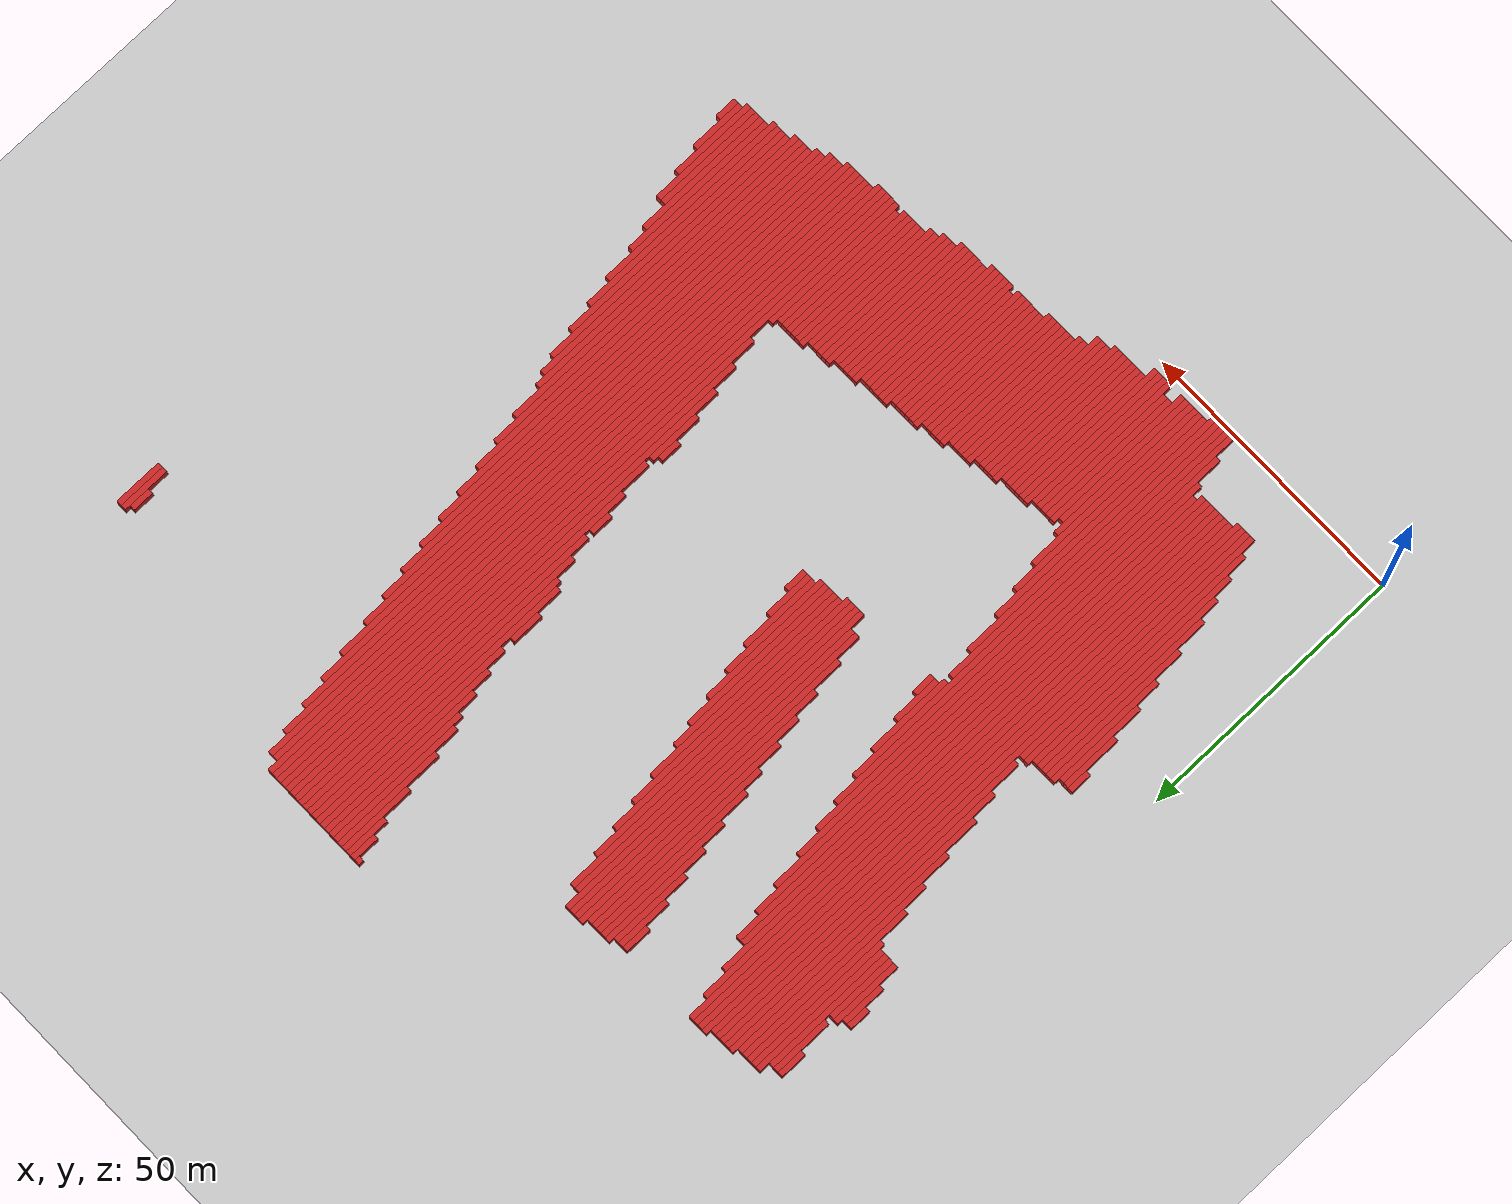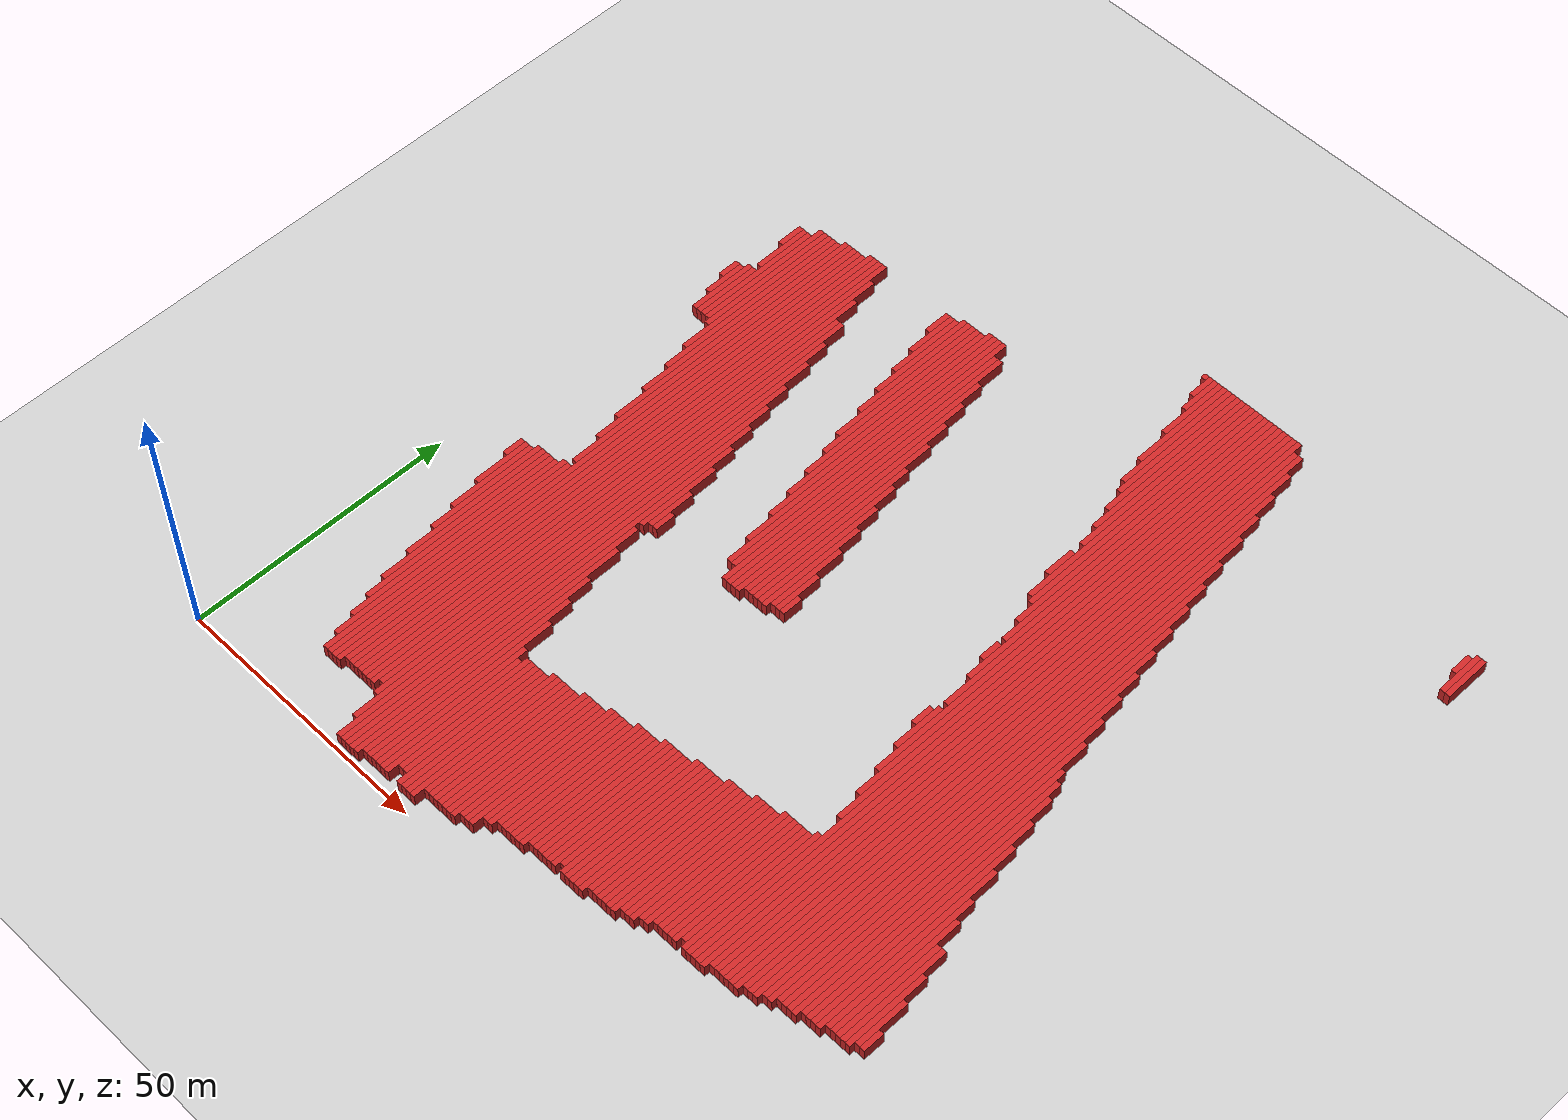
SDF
<?xml version='1.0'?>
        <sdf version='1.4'>
            <world name='1_wall'>
                <light name='sun' type='directional'>
                    <cast_shadows>1</cast_shadows>
                    <pose>0 0 10 0 -0 0</pose>
                    <diffuse>0.8 0.8 0.8 1</diffuse>
                    <specular>0.2 0.2 0.2 1</specular>
                    <attenuation>
                    <range>1000</range>
                    <constant>0.9</constant>
                    <linear>0.01</linear>
                    <quadratic>0.001</quadratic>
                    </attenuation>
                    <direction>-0.5 0.1 -0.9</direction>
                </light>
                <model name='ground_plane'>
                    <static>1</static>
                    <link name='link'>
                        <collision name='collision'>
                        <geometry>
                            <plane>
                                <normal>0 0 1</normal>
                                <size>1000 1000</size>
                            </plane>
                        </geometry>
                        <surface>
                            <friction>
                                <ode>
                                    <mu>100</mu>
                                    <mu2>50</mu2>
                                </ode>
                            </friction>
                            <bounce/>
                                <contact>
                                    <ode/>
                                </contact>
                        </surface>
                        <max_contacts>10</max_contacts>
                        </collision>
                    <visual name='visual'>
                        <cast_shadows>0</cast_shadows>
                        <geometry>
                            <plane>
                                <normal>0 0 1</normal>
                                <size>10000 10000</size>
                            </plane>
                            </geometry>
                                <material>
                                <script>
                                        <uri>file://media/materials/scripts/gazebo.material</uri>
                                        <name>Gazebo/Grey</name>
                                        </script>
                                    </material>
                    </visual>
                    <velocity_decay>
                        <linear>0</linear>
                        <angular>0</angular>
                    </velocity_decay>
                    <self_collide>0</self_collide>
                        <kinematic>0</kinematic>
                        <gravity>1</gravity>
                    </link>
                </model>
                <physics type='ode'>
                    <max_step_size>0.01</max_step_size>
                    <real_time_factor>1</real_time_factor>
                    <real_time_update_rate>100</real_time_update_rate>
                    <gravity>0 0 -9.8</gravity>
                </physics>
            <scene>
                <ambient>0.4 0.4 0.4 1</ambient>
                <background>0.7 0.7 0.7 1</background>
                <shadows>1</shadows>
            </scene>
    <model name='Wall_0'>
     <static>1</static>
    <link name='Wall_0'>
    <collision name='Wall_Collision_0'>
        <geometry>
          <box>
            <size>4.0 1.0 2.5</size>
          </box>
        </geometry>
        <pose>0 0 1.25 0 -0 0</pose>
      </collision>
      <visual name='Wall_Visual_0'>
        <pose>0 0 1.25 0 -0 0</pose>
        <geometry>
          <box>
            <size>4.0 1.0 2.5</size>
          </box>
        </geometry>
        <material>
          <script>
            <uri>file://media/materials/scripts/gazebo.material</uri>
            <name>Gazebo/Red</name>
          </script>
        </material>
      </visual>
      <velocity_decay>
        <linear>0</linear>
        <angular>0</angular>
      </velocity_decay>
      <pose>7.5 108.0 0 0 0 1.5707963267948966</pose>
    </link>
     </model><model name='Wall_1'>
     <static>1</static>
    <link name='Wall_1'>
    <collision name='Wall_Collision_1'>
        <geometry>
          <box>
            <size>8.0 1.0 2.5</size>
          </box>
        </geometry>
        <pose>0 0 1.25 0 -0 0</pose>
      </collision>
      <visual name='Wall_Visual_1'>
        <pose>0 0 1.25 0 -0 0</pose>
        <geometry>
          <box>
            <size>8.0 1.0 2.5</size>
          </box>
        </geometry>
        <material>
          <script>
            <uri>file://media/materials/scripts/gazebo.material</uri>
            <name>Gazebo/Red</name>
          </script>
        </material>
      </visual>
      <velocity_decay>
        <linear>0</linear>
        <angular>0</angular>
      </velocity_decay>
      <pose>8.5 106.0 0 0 0 1.5707963267948966</pose>
    </link>
     </model><model name='Wall_2'>
     <static>1</static>
    <link name='Wall_2'>
    <collision name='Wall_Collision_2'>
        <geometry>
          <box>
            <size>13.0 1.0 2.5</size>
          </box>
        </geometry>
        <pose>0 0 1.25 0 -0 0</pose>
      </collision>
      <visual name='Wall_Visual_2'>
        <pose>0 0 1.25 0 -0 0</pose>
        <geometry>
          <box>
            <size>13.0 1.0 2.5</size>
          </box>
        </geometry>
        <material>
          <script>
            <uri>file://media/materials/scripts/gazebo.material</uri>
            <name>Gazebo/Red</name>
          </script>
        </material>
      </visual>
      <velocity_decay>
        <linear>0</linear>
        <angular>0</angular>
      </velocity_decay>
      <pose>9.5 104.5 0 0 0 1.5707963267948966</pose>
    </link>
     </model><model name='Wall_3'>
     <static>1</static>
    <link name='Wall_3'>
    <collision name='Wall_Collision_3'>
        <geometry>
          <box>
            <size>5.0 1.0 2.5</size>
          </box>
        </geometry>
        <pose>0 0 1.25 0 -0 0</pose>
      </collision>
      <visual name='Wall_Visual_3'>
        <pose>0 0 1.25 0 -0 0</pose>
        <geometry>
          <box>
            <size>5.0 1.0 2.5</size>
          </box>
        </geometry>
        <material>
          <script>
            <uri>file://media/materials/scripts/gazebo.material</uri>
            <name>Gazebo/Red</name>
          </script>
        </material>
      </visual>
      <velocity_decay>
        <linear>0</linear>
        <angular>0</angular>
      </velocity_decay>
      <pose>9.5 120.5 0 0 0 1.5707963267948966</pose>
    </link>
     </model><model name='Wall_4'>
     <static>1</static>
    <link name='Wall_4'>
    <collision name='Wall_Collision_4'>
        <geometry>
          <box>
            <size>4.0 1.0 2.5</size>
          </box>
        </geometry>
        <pose>0 0 1.25 0 -0 0</pose>
      </collision>
      <visual name='Wall_Visual_4'>
        <pose>0 0 1.25 0 -0 0</pose>
        <geometry>
          <box>
            <size>4.0 1.0 2.5</size>
          </box>
        </geometry>
        <material>
          <script>
            <uri>file://media/materials/scripts/gazebo.material</uri>
            <name>Gazebo/Red</name>
          </script>
        </material>
      </visual>
      <velocity_decay>
        <linear>0</linear>
        <angular>0</angular>
      </velocity_decay>
      <pose>10.5 57.0 0 0 0 1.5707963267948966</pose>
    </link>
     </model><model name='Wall_5'>
     <static>1</static>
    <link name='Wall_5'>
    <collision name='Wall_Collision_5'>
        <geometry>
          <box>
            <size>13.0 1.0 2.5</size>
          </box>
        </geometry>
        <pose>0 0 1.25 0 -0 0</pose>
      </collision>
      <visual name='Wall_Visual_5'>
        <pose>0 0 1.25 0 -0 0</pose>
        <geometry>
          <box>
            <size>13.0 1.0 2.5</size>
          </box>
        </geometry>
        <material>
          <script>
            <uri>file://media/materials/scripts/gazebo.material</uri>
            <name>Gazebo/Red</name>
          </script>
        </material>
      </visual>
      <velocity_decay>
        <linear>0</linear>
        <angular>0</angular>
      </velocity_decay>
      <pose>10.5 104.5 0 0 0 1.5707963267948966</pose>
    </link>
     </model><model name='Wall_6'>
     <static>1</static>
    <link name='Wall_6'>
    <collision name='Wall_Collision_6'>
        <geometry>
          <box>
            <size>11.0 1.0 2.5</size>
          </box>
        </geometry>
        <pose>0 0 1.25 0 -0 0</pose>
      </collision>
      <visual name='Wall_Visual_6'>
        <pose>0 0 1.25 0 -0 0</pose>
        <geometry>
          <box>
            <size>11.0 1.0 2.5</size>
          </box>
        </geometry>
        <material>
          <script>
            <uri>file://media/materials/scripts/gazebo.material</uri>
            <name>Gazebo/Red</name>
          </script>
        </material>
      </visual>
      <velocity_decay>
        <linear>0</linear>
        <angular>0</angular>
      </velocity_decay>
      <pose>10.5 117.5 0 0 0 1.5707963267948966</pose>
    </link>
     </model><model name='Wall_7'>
     <static>1</static>
    <link name='Wall_7'>
    <collision name='Wall_Collision_7'>
        <geometry>
          <box>
            <size>11.0 1.0 2.5</size>
          </box>
        </geometry>
        <pose>0 0 1.25 0 -0 0</pose>
      </collision>
      <visual name='Wall_Visual_7'>
        <pose>0 0 1.25 0 -0 0</pose>
        <geometry>
          <box>
            <size>11.0 1.0 2.5</size>
          </box>
        </geometry>
        <material>
          <script>
            <uri>file://media/materials/scripts/gazebo.material</uri>
            <name>Gazebo/Red</name>
          </script>
        </material>
      </visual>
      <velocity_decay>
        <linear>0</linear>
        <angular>0</angular>
      </velocity_decay>
      <pose>11.5 53.5 0 0 0 1.5707963267948966</pose>
    </link>
     </model><model name='Wall_8'>
     <static>1</static>
    <link name='Wall_8'>
    <collision name='Wall_Collision_8'>
        <geometry>
          <box>
            <size>25.0 1.0 2.5</size>
          </box>
        </geometry>
        <pose>0 0 1.25 0 -0 0</pose>
      </collision>
      <visual name='Wall_Visual_8'>
        <pose>0 0 1.25 0 -0 0</pose>
        <geometry>
          <box>
            <size>25.0 1.0 2.5</size>
          </box>
        </geometry>
        <material>
          <script>
            <uri>file://media/materials/scripts/gazebo.material</uri>
            <name>Gazebo/Red</name>
          </script>
        </material>
      </visual>
      <velocity_decay>
        <linear>0</linear>
        <angular>0</angular>
      </velocity_decay>
      <pose>11.5 110.5 0 0 0 1.5707963267948966</pose>
    </link>
     </model><model name='Wall_9'>
     <static>1</static>
    <link name='Wall_9'>
    <collision name='Wall_Collision_9'>
        <geometry>
          <box>
            <size>17.0 1.0 2.5</size>
          </box>
        </geometry>
        <pose>0 0 1.25 0 -0 0</pose>
      </collision>
      <visual name='Wall_Visual_9'>
        <pose>0 0 1.25 0 -0 0</pose>
        <geometry>
          <box>
            <size>17.0 1.0 2.5</size>
          </box>
        </geometry>
        <material>
          <script>
            <uri>file://media/materials/scripts/gazebo.material</uri>
            <name>Gazebo/Red</name>
          </script>
        </material>
      </visual>
      <velocity_decay>
        <linear>0</linear>
        <angular>0</angular>
      </velocity_decay>
      <pose>12.5 50.5 0 0 0 1.5707963267948966</pose>
    </link>
     </model><model name='Wall_10'>
     <static>1</static>
    <link name='Wall_10'>
    <collision name='Wall_Collision_10'>
        <geometry>
          <box>
            <size>27.0 1.0 2.5</size>
          </box>
        </geometry>
        <pose>0 0 1.25 0 -0 0</pose>
      </collision>
      <visual name='Wall_Visual_10'>
        <pose>0 0 1.25 0 -0 0</pose>
        <geometry>
          <box>
            <size>27.0 1.0 2.5</size>
          </box>
        </geometry>
        <material>
          <script>
            <uri>file://media/materials/scripts/gazebo.material</uri>
            <name>Gazebo/Red</name>
          </script>
        </material>
      </visual>
      <velocity_decay>
        <linear>0</linear>
        <angular>0</angular>
      </velocity_decay>
      <pose>12.5 111.5 0 0 0 1.5707963267948966</pose>
    </link>
     </model><model name='Wall_11'>
     <static>1</static>
    <link name='Wall_11'>
    <collision name='Wall_Collision_11'>
        <geometry>
          <box>
            <size>23.0 1.0 2.5</size>
          </box>
        </geometry>
        <pose>0 0 1.25 0 -0 0</pose>
      </collision>
      <visual name='Wall_Visual_11'>
        <pose>0 0 1.25 0 -0 0</pose>
        <geometry>
          <box>
            <size>23.0 1.0 2.5</size>
          </box>
        </geometry>
        <material>
          <script>
            <uri>file://media/materials/scripts/gazebo.material</uri>
            <name>Gazebo/Red</name>
          </script>
        </material>
      </visual>
      <velocity_decay>
        <linear>0</linear>
        <angular>0</angular>
      </velocity_decay>
      <pose>13.5 48.5 0 0 0 1.5707963267948966</pose>
    </link>
     </model><model name='Wall_12'>
     <static>1</static>
    <link name='Wall_12'>
    <collision name='Wall_Collision_12'>
        <geometry>
          <box>
            <size>28.0 1.0 2.5</size>
          </box>
        </geometry>
        <pose>0 0 1.25 0 -0 0</pose>
      </collision>
      <visual name='Wall_Visual_12'>
        <pose>0 0 1.25 0 -0 0</pose>
        <geometry>
          <box>
            <size>28.0 1.0 2.5</size>
          </box>
        </geometry>
        <material>
          <script>
            <uri>file://media/materials/scripts/gazebo.material</uri>
            <name>Gazebo/Red</name>
          </script>
        </material>
      </visual>
      <velocity_decay>
        <linear>0</linear>
        <angular>0</angular>
      </velocity_decay>
      <pose>13.5 111.0 0 0 0 1.5707963267948966</pose>
    </link>
     </model><model name='Wall_13'>
     <static>1</static>
    <link name='Wall_13'>
    <collision name='Wall_Collision_13'>
        <geometry>
          <box>
            <size>29.0 1.0 2.5</size>
          </box>
        </geometry>
        <pose>0 0 1.25 0 -0 0</pose>
      </collision>
      <visual name='Wall_Visual_13'>
        <pose>0 0 1.25 0 -0 0</pose>
        <geometry>
          <box>
            <size>29.0 1.0 2.5</size>
          </box>
        </geometry>
        <material>
          <script>
            <uri>file://media/materials/scripts/gazebo.material</uri>
            <name>Gazebo/Red</name>
          </script>
        </material>
      </visual>
      <velocity_decay>
        <linear>0</linear>
        <angular>0</angular>
      </velocity_decay>
      <pose>14.5 45.5 0 0 0 1.5707963267948966</pose>
    </link>
     </model><model name='Wall_14'>
     <static>1</static>
    <link name='Wall_14'>
    <collision name='Wall_Collision_14'>
        <geometry>
          <box>
            <size>34.0 1.0 2.5</size>
          </box>
        </geometry>
        <pose>0 0 1.25 0 -0 0</pose>
      </collision>
      <visual name='Wall_Visual_14'>
        <pose>0 0 1.25 0 -0 0</pose>
        <geometry>
          <box>
            <size>34.0 1.0 2.5</size>
          </box>
        </geometry>
        <material>
          <script>
            <uri>file://media/materials/scripts/gazebo.material</uri>
            <name>Gazebo/Red</name>
          </script>
        </material>
      </visual>
      <velocity_decay>
        <linear>0</linear>
        <angular>0</angular>
      </velocity_decay>
      <pose>14.5 108.0 0 0 0 1.5707963267948966</pose>
    </link>
     </model><model name='Wall_15'>
     <static>1</static>
    <link name='Wall_15'>
    <collision name='Wall_Collision_15'>
        <geometry>
          <box>
            <size>35.0 1.0 2.5</size>
          </box>
        </geometry>
        <pose>0 0 1.25 0 -0 0</pose>
      </collision>
      <visual name='Wall_Visual_15'>
        <pose>0 0 1.25 0 -0 0</pose>
        <geometry>
          <box>
            <size>35.0 1.0 2.5</size>
          </box>
        </geometry>
        <material>
          <script>
            <uri>file://media/materials/scripts/gazebo.material</uri>
            <name>Gazebo/Red</name>
          </script>
        </material>
      </visual>
      <velocity_decay>
        <linear>0</linear>
        <angular>0</angular>
      </velocity_decay>
      <pose>15.5 42.5 0 0 0 1.5707963267948966</pose>
    </link>
     </model><model name='Wall_16'>
     <static>1</static>
    <link name='Wall_16'>
    <collision name='Wall_Collision_16'>
        <geometry>
          <box>
            <size>39.0 1.0 2.5</size>
          </box>
        </geometry>
        <pose>0 0 1.25 0 -0 0</pose>
      </collision>
      <visual name='Wall_Visual_16'>
        <pose>0 0 1.25 0 -0 0</pose>
        <geometry>
          <box>
            <size>39.0 1.0 2.5</size>
          </box>
        </geometry>
        <material>
          <script>
            <uri>file://media/materials/scripts/gazebo.material</uri>
            <name>Gazebo/Red</name>
          </script>
        </material>
      </visual>
      <velocity_decay>
        <linear>0</linear>
        <angular>0</angular>
      </velocity_decay>
      <pose>15.5 105.5 0 0 0 1.5707963267948966</pose>
    </link>
     </model><model name='Wall_17'>
     <static>1</static>
    <link name='Wall_17'>
    <collision name='Wall_Collision_17'>
        <geometry>
          <box>
            <size>39.0 1.0 2.5</size>
          </box>
        </geometry>
        <pose>0 0 1.25 0 -0 0</pose>
      </collision>
      <visual name='Wall_Visual_17'>
        <pose>0 0 1.25 0 -0 0</pose>
        <geometry>
          <box>
            <size>39.0 1.0 2.5</size>
          </box>
        </geometry>
        <material>
          <script>
            <uri>file://media/materials/scripts/gazebo.material</uri>
            <name>Gazebo/Red</name>
          </script>
        </material>
      </visual>
      <velocity_decay>
        <linear>0</linear>
        <angular>0</angular>
      </velocity_decay>
      <pose>16.5 40.5 0 0 0 1.5707963267948966</pose>
    </link>
     </model><model name='Wall_18'>
     <static>1</static>
    <link name='Wall_18'>
    <collision name='Wall_Collision_18'>
        <geometry>
          <box>
            <size>45.0 1.0 2.5</size>
          </box>
        </geometry>
        <pose>0 0 1.25 0 -0 0</pose>
      </collision>
      <visual name='Wall_Visual_18'>
        <pose>0 0 1.25 0 -0 0</pose>
        <geometry>
          <box>
            <size>45.0 1.0 2.5</size>
          </box>
        </geometry>
        <material>
          <script>
            <uri>file://media/materials/scripts/gazebo.material</uri>
            <name>Gazebo/Red</name>
          </script>
        </material>
      </visual>
      <velocity_decay>
        <linear>0</linear>
        <angular>0</angular>
      </velocity_decay>
      <pose>16.5 102.5 0 0 0 1.5707963267948966</pose>
    </link>
     </model><model name='Wall_19'>
     <static>1</static>
    <link name='Wall_19'>
    <collision name='Wall_Collision_19'>
        <geometry>
          <box>
            <size>43.0 1.0 2.5</size>
          </box>
        </geometry>
        <pose>0 0 1.25 0 -0 0</pose>
      </collision>
      <visual name='Wall_Visual_19'>
        <pose>0 0 1.25 0 -0 0</pose>
        <geometry>
          <box>
            <size>43.0 1.0 2.5</size>
          </box>
        </geometry>
        <material>
          <script>
            <uri>file://media/materials/scripts/gazebo.material</uri>
            <name>Gazebo/Red</name>
          </script>
        </material>
      </visual>
      <velocity_decay>
        <linear>0</linear>
        <angular>0</angular>
      </velocity_decay>
      <pose>17.5 38.5 0 0 0 1.5707963267948966</pose>
    </link>
     </model><model name='Wall_20'>
     <static>1</static>
    <link name='Wall_20'>
    <collision name='Wall_Collision_20'>
        <geometry>
          <box>
            <size>53.0 1.0 2.5</size>
          </box>
        </geometry>
        <pose>0 0 1.25 0 -0 0</pose>
      </collision>
      <visual name='Wall_Visual_20'>
        <pose>0 0 1.25 0 -0 0</pose>
        <geometry>
          <box>
            <size>53.0 1.0 2.5</size>
          </box>
        </geometry>
        <material>
          <script>
            <uri>file://media/materials/scripts/gazebo.material</uri>
            <name>Gazebo/Red</name>
          </script>
        </material>
      </visual>
      <velocity_decay>
        <linear>0</linear>
        <angular>0</angular>
      </velocity_decay>
      <pose>17.5 99.5 0 0 0 1.5707963267948966</pose>
    </link>
     </model><model name='Wall_21'>
     <static>1</static>
    <link name='Wall_21'>
    <collision name='Wall_Collision_21'>
        <geometry>
          <box>
            <size>48.0 1.0 2.5</size>
          </box>
        </geometry>
        <pose>0 0 1.25 0 -0 0</pose>
      </collision>
      <visual name='Wall_Visual_21'>
        <pose>0 0 1.25 0 -0 0</pose>
        <geometry>
          <box>
            <size>48.0 1.0 2.5</size>
          </box>
        </geometry>
        <material>
          <script>
            <uri>file://media/materials/scripts/gazebo.material</uri>
            <name>Gazebo/Red</name>
          </script>
        </material>
      </visual>
      <velocity_decay>
        <linear>0</linear>
        <angular>0</angular>
      </velocity_decay>
      <pose>18.5 37.0 0 0 0 1.5707963267948966</pose>
    </link>
     </model><model name='Wall_22'>
     <static>1</static>
    <link name='Wall_22'>
    <collision name='Wall_Collision_22'>
        <geometry>
          <box>
            <size>58.0 1.0 2.5</size>
          </box>
        </geometry>
        <pose>0 0 1.25 0 -0 0</pose>
      </collision>
      <visual name='Wall_Visual_22'>
        <pose>0 0 1.25 0 -0 0</pose>
        <geometry>
          <box>
            <size>58.0 1.0 2.5</size>
          </box>
        </geometry>
        <material>
          <script>
            <uri>file://media/materials/scripts/gazebo.material</uri>
            <name>Gazebo/Red</name>
          </script>
        </material>
      </visual>
      <velocity_decay>
        <linear>0</linear>
        <angular>0</angular>
      </velocity_decay>
      <pose>18.5 97.0 0 0 0 1.5707963267948966</pose>
    </link>
     </model><model name='Wall_23'>
     <static>1</static>
    <link name='Wall_23'>
    <collision name='Wall_Collision_23'>
        <geometry>
          <box>
            <size>51.0 1.0 2.5</size>
          </box>
        </geometry>
        <pose>0 0 1.25 0 -0 0</pose>
      </collision>
      <visual name='Wall_Visual_23'>
        <pose>0 0 1.25 0 -0 0</pose>
        <geometry>
          <box>
            <size>51.0 1.0 2.5</size>
          </box>
        </geometry>
        <material>
          <script>
            <uri>file://media/materials/scripts/gazebo.material</uri>
            <name>Gazebo/Red</name>
          </script>
        </material>
      </visual>
      <velocity_decay>
        <linear>0</linear>
        <angular>0</angular>
      </velocity_decay>
      <pose>19.5 35.5 0 0 0 1.5707963267948966</pose>
    </link>
     </model><model name='Wall_24'>
     <static>1</static>
    <link name='Wall_24'>
    <collision name='Wall_Collision_24'>
        <geometry>
          <box>
            <size>64.0 1.0 2.5</size>
          </box>
        </geometry>
        <pose>0 0 1.25 0 -0 0</pose>
      </collision>
      <visual name='Wall_Visual_24'>
        <pose>0 0 1.25 0 -0 0</pose>
        <geometry>
          <box>
            <size>64.0 1.0 2.5</size>
          </box>
        </geometry>
        <material>
          <script>
            <uri>file://media/materials/scripts/gazebo.material</uri>
            <name>Gazebo/Red</name>
          </script>
        </material>
      </visual>
      <velocity_decay>
        <linear>0</linear>
        <angular>0</angular>
      </velocity_decay>
      <pose>19.5 94.0 0 0 0 1.5707963267948966</pose>
    </link>
     </model><model name='Wall_25'>
     <static>1</static>
    <link name='Wall_25'>
    <collision name='Wall_Collision_25'>
        <geometry>
          <box>
            <size>116.0 1.0 2.5</size>
          </box>
        </geometry>
        <pose>0 0 1.25 0 -0 0</pose>
      </collision>
      <visual name='Wall_Visual_25'>
        <pose>0 0 1.25 0 -0 0</pose>
        <geometry>
          <box>
            <size>116.0 1.0 2.5</size>
          </box>
        </geometry>
        <material>
          <script>
            <uri>file://media/materials/scripts/gazebo.material</uri>
            <name>Gazebo/Red</name>
          </script>
        </material>
      </visual>
      <velocity_decay>
        <linear>0</linear>
        <angular>0</angular>
      </velocity_decay>
      <pose>20.5 68.0 0 0 0 1.5707963267948966</pose>
    </link>
     </model><model name='Wall_26'>
     <static>1</static>
    <link name='Wall_26'>
    <collision name='Wall_Collision_26'>
        <geometry>
          <box>
            <size>116.0 1.0 2.5</size>
          </box>
        </geometry>
        <pose>0 0 1.25 0 -0 0</pose>
      </collision>
      <visual name='Wall_Visual_26'>
        <pose>0 0 1.25 0 -0 0</pose>
        <geometry>
          <box>
            <size>116.0 1.0 2.5</size>
          </box>
        </geometry>
        <material>
          <script>
            <uri>file://media/materials/scripts/gazebo.material</uri>
            <name>Gazebo/Red</name>
          </script>
        </material>
      </visual>
      <velocity_decay>
        <linear>0</linear>
        <angular>0</angular>
      </velocity_decay>
      <pose>21.5 68.0 0 0 0 1.5707963267948966</pose>
    </link>
     </model><model name='Wall_27'>
     <static>1</static>
    <link name='Wall_27'>
    <collision name='Wall_Collision_27'>
        <geometry>
          <box>
            <size>117.0 1.0 2.5</size>
          </box>
        </geometry>
        <pose>0 0 1.25 0 -0 0</pose>
      </collision>
      <visual name='Wall_Visual_27'>
        <pose>0 0 1.25 0 -0 0</pose>
        <geometry>
          <box>
            <size>117.0 1.0 2.5</size>
          </box>
        </geometry>
        <material>
          <script>
            <uri>file://media/materials/scripts/gazebo.material</uri>
            <name>Gazebo/Red</name>
          </script>
        </material>
      </visual>
      <velocity_decay>
        <linear>0</linear>
        <angular>0</angular>
      </velocity_decay>
      <pose>22.5 68.5 0 0 0 1.5707963267948966</pose>
    </link>
     </model><model name='Wall_28'>
     <static>1</static>
    <link name='Wall_28'>
    <collision name='Wall_Collision_28'>
        <geometry>
          <box>
            <size>116.0 1.0 2.5</size>
          </box>
        </geometry>
        <pose>0 0 1.25 0 -0 0</pose>
      </collision>
      <visual name='Wall_Visual_28'>
        <pose>0 0 1.25 0 -0 0</pose>
        <geometry>
          <box>
            <size>116.0 1.0 2.5</size>
          </box>
        </geometry>
        <material>
          <script>
            <uri>file://media/materials/scripts/gazebo.material</uri>
            <name>Gazebo/Red</name>
          </script>
        </material>
      </visual>
      <velocity_decay>
        <linear>0</linear>
        <angular>0</angular>
      </velocity_decay>
      <pose>23.5 69.0 0 0 0 1.5707963267948966</pose>
    </link>
     </model><model name='Wall_29'>
     <static>1</static>
    <link name='Wall_29'>
    <collision name='Wall_Collision_29'>
        <geometry>
          <box>
            <size>116.0 1.0 2.5</size>
          </box>
        </geometry>
        <pose>0 0 1.25 0 -0 0</pose>
      </collision>
      <visual name='Wall_Visual_29'>
        <pose>0 0 1.25 0 -0 0</pose>
        <geometry>
          <box>
            <size>116.0 1.0 2.5</size>
          </box>
        </geometry>
        <material>
          <script>
            <uri>file://media/materials/scripts/gazebo.material</uri>
            <name>Gazebo/Red</name>
          </script>
        </material>
      </visual>
      <velocity_decay>
        <linear>0</linear>
        <angular>0</angular>
      </velocity_decay>
      <pose>24.5 69.0 0 0 0 1.5707963267948966</pose>
    </link>
     </model><model name='Wall_30'>
     <static>1</static>
    <link name='Wall_30'>
    <collision name='Wall_Collision_30'>
        <geometry>
          <box>
            <size>116.0 1.0 2.5</size>
          </box>
        </geometry>
        <pose>0 0 1.25 0 -0 0</pose>
      </collision>
      <visual name='Wall_Visual_30'>
        <pose>0 0 1.25 0 -0 0</pose>
        <geometry>
          <box>
            <size>116.0 1.0 2.5</size>
          </box>
        </geometry>
        <material>
          <script>
            <uri>file://media/materials/scripts/gazebo.material</uri>
            <name>Gazebo/Red</name>
          </script>
        </material>
      </visual>
      <velocity_decay>
        <linear>0</linear>
        <angular>0</angular>
      </velocity_decay>
      <pose>25.5 69.0 0 0 0 1.5707963267948966</pose>
    </link>
     </model><model name='Wall_31'>
     <static>1</static>
    <link name='Wall_31'>
    <collision name='Wall_Collision_31'>
        <geometry>
          <box>
            <size>112.0 1.0 2.5</size>
          </box>
        </geometry>
        <pose>0 0 1.25 0 -0 0</pose>
      </collision>
      <visual name='Wall_Visual_31'>
        <pose>0 0 1.25 0 -0 0</pose>
        <geometry>
          <box>
            <size>112.0 1.0 2.5</size>
          </box>
        </geometry>
        <material>
          <script>
            <uri>file://media/materials/scripts/gazebo.material</uri>
            <name>Gazebo/Red</name>
          </script>
        </material>
      </visual>
      <velocity_decay>
        <linear>0</linear>
        <angular>0</angular>
      </velocity_decay>
      <pose>26.5 67.0 0 0 0 1.5707963267948966</pose>
    </link>
     </model><model name='Wall_32'>
     <static>1</static>
    <link name='Wall_32'>
    <collision name='Wall_Collision_32'>
        <geometry>
          <box>
            <size>107.0 1.0 2.5</size>
          </box>
        </geometry>
        <pose>0 0 1.25 0 -0 0</pose>
      </collision>
      <visual name='Wall_Visual_32'>
        <pose>0 0 1.25 0 -0 0</pose>
        <geometry>
          <box>
            <size>107.0 1.0 2.5</size>
          </box>
        </geometry>
        <material>
          <script>
            <uri>file://media/materials/scripts/gazebo.material</uri>
            <name>Gazebo/Red</name>
          </script>
        </material>
      </visual>
      <velocity_decay>
        <linear>0</linear>
        <angular>0</angular>
      </velocity_decay>
      <pose>27.5 64.5 0 0 0 1.5707963267948966</pose>
    </link>
     </model><model name='Wall_33'>
     <static>1</static>
    <link name='Wall_33'>
    <collision name='Wall_Collision_33'>
        <geometry>
          <box>
            <size>102.0 1.0 2.5</size>
          </box>
        </geometry>
        <pose>0 0 1.25 0 -0 0</pose>
      </collision>
      <visual name='Wall_Visual_33'>
        <pose>0 0 1.25 0 -0 0</pose>
        <geometry>
          <box>
            <size>102.0 1.0 2.5</size>
          </box>
        </geometry>
        <material>
          <script>
            <uri>file://media/materials/scripts/gazebo.material</uri>
            <name>Gazebo/Red</name>
          </script>
        </material>
      </visual>
      <velocity_decay>
        <linear>0</linear>
        <angular>0</angular>
      </velocity_decay>
      <pose>28.5 62.0 0 0 0 1.5707963267948966</pose>
    </link>
     </model><model name='Wall_34'>
     <static>1</static>
    <link name='Wall_34'>
    <collision name='Wall_Collision_34'>
        <geometry>
          <box>
            <size>102.0 1.0 2.5</size>
          </box>
        </geometry>
        <pose>0 0 1.25 0 -0 0</pose>
      </collision>
      <visual name='Wall_Visual_34'>
        <pose>0 0 1.25 0 -0 0</pose>
        <geometry>
          <box>
            <size>102.0 1.0 2.5</size>
          </box>
        </geometry>
        <material>
          <script>
            <uri>file://media/materials/scripts/gazebo.material</uri>
            <name>Gazebo/Red</name>
          </script>
        </material>
      </visual>
      <velocity_decay>
        <linear>0</linear>
        <angular>0</angular>
      </velocity_decay>
      <pose>29.5 62.0 0 0 0 1.5707963267948966</pose>
    </link>
     </model><model name='Wall_35'>
     <static>1</static>
    <link name='Wall_35'>
    <collision name='Wall_Collision_35'>
        <geometry>
          <box>
            <size>96.0 1.0 2.5</size>
          </box>
        </geometry>
        <pose>0 0 1.25 0 -0 0</pose>
      </collision>
      <visual name='Wall_Visual_35'>
        <pose>0 0 1.25 0 -0 0</pose>
        <geometry>
          <box>
            <size>96.0 1.0 2.5</size>
          </box>
        </geometry>
        <material>
          <script>
            <uri>file://media/materials/scripts/gazebo.material</uri>
            <name>Gazebo/Red</name>
          </script>
        </material>
      </visual>
      <velocity_decay>
        <linear>0</linear>
        <angular>0</angular>
      </velocity_decay>
      <pose>30.5 60.0 0 0 0 1.5707963267948966</pose>
    </link>
     </model><model name='Wall_36'>
     <static>1</static>
    <link name='Wall_36'>
    <collision name='Wall_Collision_36'>
        <geometry>
          <box>
            <size>93.0 1.0 2.5</size>
          </box>
        </geometry>
        <pose>0 0 1.25 0 -0 0</pose>
      </collision>
      <visual name='Wall_Visual_36'>
        <pose>0 0 1.25 0 -0 0</pose>
        <geometry>
          <box>
            <size>93.0 1.0 2.5</size>
          </box>
        </geometry>
        <material>
          <script>
            <uri>file://media/materials/scripts/gazebo.material</uri>
            <name>Gazebo/Red</name>
          </script>
        </material>
      </visual>
      <velocity_decay>
        <linear>0</linear>
        <angular>0</angular>
      </velocity_decay>
      <pose>31.5 56.5 0 0 0 1.5707963267948966</pose>
    </link>
     </model><model name='Wall_37'>
     <static>1</static>
    <link name='Wall_37'>
    <collision name='Wall_Collision_37'>
        <geometry>
          <box>
            <size>92.0 1.0 2.5</size>
          </box>
        </geometry>
        <pose>0 0 1.25 0 -0 0</pose>
      </collision>
      <visual name='Wall_Visual_37'>
        <pose>0 0 1.25 0 -0 0</pose>
        <geometry>
          <box>
            <size>92.0 1.0 2.5</size>
          </box>
        </geometry>
        <material>
          <script>
            <uri>file://media/materials/scripts/gazebo.material</uri>
            <name>Gazebo/Red</name>
          </script>
        </material>
      </visual>
      <velocity_decay>
        <linear>0</linear>
        <angular>0</angular>
      </velocity_decay>
      <pose>32.5 51.0 0 0 0 1.5707963267948966</pose>
    </link>
     </model><model name='Wall_38'>
     <static>1</static>
    <link name='Wall_38'>
    <collision name='Wall_Collision_38'>
        <geometry>
          <box>
            <size>91.0 1.0 2.5</size>
          </box>
        </geometry>
        <pose>0 0 1.25 0 -0 0</pose>
      </collision>
      <visual name='Wall_Visual_38'>
        <pose>0 0 1.25 0 -0 0</pose>
        <geometry>
          <box>
            <size>91.0 1.0 2.5</size>
          </box>
        </geometry>
        <material>
          <script>
            <uri>file://media/materials/scripts/gazebo.material</uri>
            <name>Gazebo/Red</name>
          </script>
        </material>
      </visual>
      <velocity_decay>
        <linear>0</linear>
        <angular>0</angular>
      </velocity_decay>
      <pose>33.5 46.5 0 0 0 1.5707963267948966</pose>
    </link>
     </model><model name='Wall_39'>
     <static>1</static>
    <link name='Wall_39'>
    <collision name='Wall_Collision_39'>
        <geometry>
          <box>
            <size>86.0 1.0 2.5</size>
          </box>
        </geometry>
        <pose>0 0 1.25 0 -0 0</pose>
      </collision>
      <visual name='Wall_Visual_39'>
        <pose>0 0 1.25 0 -0 0</pose>
        <geometry>
          <box>
            <size>86.0 1.0 2.5</size>
          </box>
        </geometry>
        <material>
          <script>
            <uri>file://media/materials/scripts/gazebo.material</uri>
            <name>Gazebo/Red</name>
          </script>
        </material>
      </visual>
      <velocity_decay>
        <linear>0</linear>
        <angular>0</angular>
      </velocity_decay>
      <pose>34.5 44.0 0 0 0 1.5707963267948966</pose>
    </link>
     </model><model name='Wall_40'>
     <static>1</static>
    <link name='Wall_40'>
    <collision name='Wall_Collision_40'>
        <geometry>
          <box>
            <size>81.0 1.0 2.5</size>
          </box>
        </geometry>
        <pose>0 0 1.25 0 -0 0</pose>
      </collision>
      <visual name='Wall_Visual_40'>
        <pose>0 0 1.25 0 -0 0</pose>
        <geometry>
          <box>
            <size>81.0 1.0 2.5</size>
          </box>
        </geometry>
        <material>
          <script>
            <uri>file://media/materials/scripts/gazebo.material</uri>
            <name>Gazebo/Red</name>
          </script>
        </material>
      </visual>
      <velocity_decay>
        <linear>0</linear>
        <angular>0</angular>
      </velocity_decay>
      <pose>35.5 41.5 0 0 0 1.5707963267948966</pose>
    </link>
     </model><model name='Wall_41'>
     <static>1</static>
    <link name='Wall_41'>
    <collision name='Wall_Collision_41'>
        <geometry>
          <box>
            <size>59.0 1.0 2.5</size>
          </box>
        </geometry>
        <pose>0 0 1.25 0 -0 0</pose>
      </collision>
      <visual name='Wall_Visual_41'>
        <pose>0 0 1.25 0 -0 0</pose>
        <geometry>
          <box>
            <size>59.0 1.0 2.5</size>
          </box>
        </geometry>
        <material>
          <script>
            <uri>file://media/materials/scripts/gazebo.material</uri>
            <name>Gazebo/Red</name>
          </script>
        </material>
      </visual>
      <velocity_decay>
        <linear>0</linear>
        <angular>0</angular>
      </velocity_decay>
      <pose>36.5 30.5 0 0 0 1.5707963267948966</pose>
    </link>
     </model><model name='Wall_42'>
     <static>1</static>
    <link name='Wall_42'>
    <collision name='Wall_Collision_42'>
        <geometry>
          <box>
            <size>16.0 1.0 2.5</size>
          </box>
        </geometry>
        <pose>0 0 1.25 0 -0 0</pose>
      </collision>
      <visual name='Wall_Visual_42'>
        <pose>0 0 1.25 0 -0 0</pose>
        <geometry>
          <box>
            <size>16.0 1.0 2.5</size>
          </box>
        </geometry>
        <material>
          <script>
            <uri>file://media/materials/scripts/gazebo.material</uri>
            <name>Gazebo/Red</name>
          </script>
        </material>
      </visual>
      <velocity_decay>
        <linear>0</linear>
        <angular>0</angular>
      </velocity_decay>
      <pose>36.5 69.0 0 0 0 1.5707963267948966</pose>
    </link>
     </model><model name='Wall_43'>
     <static>1</static>
    <link name='Wall_43'>
    <collision name='Wall_Collision_43'>
        <geometry>
          <box>
            <size>54.0 1.0 2.5</size>
          </box>
        </geometry>
        <pose>0 0 1.25 0 -0 0</pose>
      </collision>
      <visual name='Wall_Visual_43'>
        <pose>0 0 1.25 0 -0 0</pose>
        <geometry>
          <box>
            <size>54.0 1.0 2.5</size>
          </box>
        </geometry>
        <material>
          <script>
            <uri>file://media/materials/scripts/gazebo.material</uri>
            <name>Gazebo/Red</name>
          </script>
        </material>
      </visual>
      <velocity_decay>
        <linear>0</linear>
        <angular>0</angular>
      </velocity_decay>
      <pose>37.5 28.0 0 0 0 1.5707963267948966</pose>
    </link>
     </model><model name='Wall_44'>
     <static>1</static>
    <link name='Wall_44'>
    <collision name='Wall_Collision_44'>
        <geometry>
          <box>
            <size>9.0 1.0 2.5</size>
          </box>
        </geometry>
        <pose>0 0 1.25 0 -0 0</pose>
      </collision>
      <visual name='Wall_Visual_44'>
        <pose>0 0 1.25 0 -0 0</pose>
        <geometry>
          <box>
            <size>9.0 1.0 2.5</size>
          </box>
        </geometry>
        <material>
          <script>
            <uri>file://media/materials/scripts/gazebo.material</uri>
            <name>Gazebo/Red</name>
          </script>
        </material>
      </visual>
      <velocity_decay>
        <linear>0</linear>
        <angular>0</angular>
      </velocity_decay>
      <pose>37.5 66.5 0 0 0 1.5707963267948966</pose>
    </link>
     </model><model name='Wall_45'>
     <static>1</static>
    <link name='Wall_45'>
    <collision name='Wall_Collision_45'>
        <geometry>
          <box>
            <size>46.0 1.0 2.5</size>
          </box>
        </geometry>
        <pose>0 0 1.25 0 -0 0</pose>
      </collision>
      <visual name='Wall_Visual_45'>
        <pose>0 0 1.25 0 -0 0</pose>
        <geometry>
          <box>
            <size>46.0 1.0 2.5</size>
          </box>
        </geometry>
        <material>
          <script>
            <uri>file://media/materials/scripts/gazebo.material</uri>
            <name>Gazebo/Red</name>
          </script>
        </material>
      </visual>
      <velocity_decay>
        <linear>0</linear>
        <angular>0</angular>
      </velocity_decay>
      <pose>38.5 25.0 0 0 0 1.5707963267948966</pose>
    </link>
     </model><model name='Wall_46'>
     <static>1</static>
    <link name='Wall_46'>
    <collision name='Wall_Collision_46'>
        <geometry>
          <box>
            <size>4.0 1.0 2.5</size>
          </box>
        </geometry>
        <pose>0 0 1.25 0 -0 0</pose>
      </collision>
      <visual name='Wall_Visual_46'>
        <pose>0 0 1.25 0 -0 0</pose>
        <geometry>
          <box>
            <size>4.0 1.0 2.5</size>
          </box>
        </geometry>
        <material>
          <script>
            <uri>file://media/materials/scripts/gazebo.material</uri>
            <name>Gazebo/Red</name>
          </script>
        </material>
      </visual>
      <velocity_decay>
        <linear>0</linear>
        <angular>0</angular>
      </velocity_decay>
      <pose>38.5 64.0 0 0 0 1.5707963267948966</pose>
    </link>
     </model><model name='Wall_47'>
     <static>1</static>
    <link name='Wall_47'>
    <collision name='Wall_Collision_47'>
        <geometry>
          <box>
            <size>41.0 1.0 2.5</size>
          </box>
        </geometry>
        <pose>0 0 1.25 0 -0 0</pose>
      </collision>
      <visual name='Wall_Visual_47'>
        <pose>0 0 1.25 0 -0 0</pose>
        <geometry>
          <box>
            <size>41.0 1.0 2.5</size>
          </box>
        </geometry>
        <material>
          <script>
            <uri>file://media/materials/scripts/gazebo.material</uri>
            <name>Gazebo/Red</name>
          </script>
        </material>
      </visual>
      <velocity_decay>
        <linear>0</linear>
        <angular>0</angular>
      </velocity_decay>
      <pose>39.5 22.5 0 0 0 1.5707963267948966</pose>
    </link>
     </model><model name='Wall_48'>
     <static>1</static>
    <link name='Wall_48'>
    <collision name='Wall_Collision_48'>
        <geometry>
          <box>
            <size>36.0 1.0 2.5</size>
          </box>
        </geometry>
        <pose>0 0 1.25 0 -0 0</pose>
      </collision>
      <visual name='Wall_Visual_48'>
        <pose>0 0 1.25 0 -0 0</pose>
        <geometry>
          <box>
            <size>36.0 1.0 2.5</size>
          </box>
        </geometry>
        <material>
          <script>
            <uri>file://media/materials/scripts/gazebo.material</uri>
            <name>Gazebo/Red</name>
          </script>
        </material>
      </visual>
      <velocity_decay>
        <linear>0</linear>
        <angular>0</angular>
      </velocity_decay>
      <pose>40.5 20.0 0 0 0 1.5707963267948966</pose>
    </link>
     </model><model name='Wall_49'>
     <static>1</static>
    <link name='Wall_49'>
    <collision name='Wall_Collision_49'>
        <geometry>
          <box>
            <size>5.0 1.0 2.5</size>
          </box>
        </geometry>
        <pose>0 0 1.25 0 -0 0</pose>
      </collision>
      <visual name='Wall_Visual_49'>
        <pose>0 0 1.25 0 -0 0</pose>
        <geometry>
          <box>
            <size>5.0 1.0 2.5</size>
          </box>
        </geometry>
        <material>
          <script>
            <uri>file://media/materials/scripts/gazebo.material</uri>
            <name>Gazebo/Red</name>
          </script>
        </material>
      </visual>
      <velocity_decay>
        <linear>0</linear>
        <angular>0</angular>
      </velocity_decay>
      <pose>40.5 124.5 0 0 0 1.5707963267948966</pose>
    </link>
     </model><model name='Wall_50'>
     <static>1</static>
    <link name='Wall_50'>
    <collision name='Wall_Collision_50'>
        <geometry>
          <box>
            <size>30.0 1.0 2.5</size>
          </box>
        </geometry>
        <pose>0 0 1.25 0 -0 0</pose>
      </collision>
      <visual name='Wall_Visual_50'>
        <pose>0 0 1.25 0 -0 0</pose>
        <geometry>
          <box>
            <size>30.0 1.0 2.5</size>
          </box>
        </geometry>
        <material>
          <script>
            <uri>file://media/materials/scripts/gazebo.material</uri>
            <name>Gazebo/Red</name>
          </script>
        </material>
      </visual>
      <velocity_decay>
        <linear>0</linear>
        <angular>0</angular>
      </velocity_decay>
      <pose>41.5 17.0 0 0 0 1.5707963267948966</pose>
    </link>
     </model><model name='Wall_51'>
     <static>1</static>
    <link name='Wall_51'>
    <collision name='Wall_Collision_51'>
        <geometry>
          <box>
            <size>10.0 1.0 2.5</size>
          </box>
        </geometry>
        <pose>0 0 1.25 0 -0 0</pose>
      </collision>
      <visual name='Wall_Visual_51'>
        <pose>0 0 1.25 0 -0 0</pose>
        <geometry>
          <box>
            <size>10.0 1.0 2.5</size>
          </box>
        </geometry>
        <material>
          <script>
            <uri>file://media/materials/scripts/gazebo.material</uri>
            <name>Gazebo/Red</name>
          </script>
        </material>
      </visual>
      <velocity_decay>
        <linear>0</linear>
        <angular>0</angular>
      </velocity_decay>
      <pose>41.5 122.0 0 0 0 1.5707963267948966</pose>
    </link>
     </model><model name='Wall_52'>
     <static>1</static>
    <link name='Wall_52'>
    <collision name='Wall_Collision_52'>
        <geometry>
          <box>
            <size>28.0 1.0 2.5</size>
          </box>
        </geometry>
        <pose>0 0 1.25 0 -0 0</pose>
      </collision>
      <visual name='Wall_Visual_52'>
        <pose>0 0 1.25 0 -0 0</pose>
        <geometry>
          <box>
            <size>28.0 1.0 2.5</size>
          </box>
        </geometry>
        <material>
          <script>
            <uri>file://media/materials/scripts/gazebo.material</uri>
            <name>Gazebo/Red</name>
          </script>
        </material>
      </visual>
      <velocity_decay>
        <linear>0</linear>
        <angular>0</angular>
      </velocity_decay>
      <pose>42.5 16.0 0 0 0 1.5707963267948966</pose>
    </link>
     </model><model name='Wall_53'>
     <static>1</static>
    <link name='Wall_53'>
    <collision name='Wall_Collision_53'>
        <geometry>
          <box>
            <size>15.0 1.0 2.5</size>
          </box>
        </geometry>
        <pose>0 0 1.25 0 -0 0</pose>
      </collision>
      <visual name='Wall_Visual_53'>
        <pose>0 0 1.25 0 -0 0</pose>
        <geometry>
          <box>
            <size>15.0 1.0 2.5</size>
          </box>
        </geometry>
        <material>
          <script>
            <uri>file://media/materials/scripts/gazebo.material</uri>
            <name>Gazebo/Red</name>
          </script>
        </material>
      </visual>
      <velocity_decay>
        <linear>0</linear>
        <angular>0</angular>
      </velocity_decay>
      <pose>42.5 119.5 0 0 0 1.5707963267948966</pose>
    </link>
     </model><model name='Wall_54'>
     <static>1</static>
    <link name='Wall_54'>
    <collision name='Wall_Collision_54'>
        <geometry>
          <box>
            <size>29.0 1.0 2.5</size>
          </box>
        </geometry>
        <pose>0 0 1.25 0 -0 0</pose>
      </collision>
      <visual name='Wall_Visual_54'>
        <pose>0 0 1.25 0 -0 0</pose>
        <geometry>
          <box>
            <size>29.0 1.0 2.5</size>
          </box>
        </geometry>
        <material>
          <script>
            <uri>file://media/materials/scripts/gazebo.material</uri>
            <name>Gazebo/Red</name>
          </script>
        </material>
      </visual>
      <velocity_decay>
        <linear>0</linear>
        <angular>0</angular>
      </velocity_decay>
      <pose>43.5 16.5 0 0 0 1.5707963267948966</pose>
    </link>
     </model><model name='Wall_55'>
     <static>1</static>
    <link name='Wall_55'>
    <collision name='Wall_Collision_55'>
        <geometry>
          <box>
            <size>21.0 1.0 2.5</size>
          </box>
        </geometry>
        <pose>0 0 1.25 0 -0 0</pose>
      </collision>
      <visual name='Wall_Visual_55'>
        <pose>0 0 1.25 0 -0 0</pose>
        <geometry>
          <box>
            <size>21.0 1.0 2.5</size>
          </box>
        </geometry>
        <material>
          <script>
            <uri>file://media/materials/scripts/gazebo.material</uri>
            <name>Gazebo/Red</name>
          </script>
        </material>
      </visual>
      <velocity_decay>
        <linear>0</linear>
        <angular>0</angular>
      </velocity_decay>
      <pose>43.5 117.5 0 0 0 1.5707963267948966</pose>
    </link>
     </model><model name='Wall_56'>
     <static>1</static>
    <link name='Wall_56'>
    <collision name='Wall_Collision_56'>
        <geometry>
          <box>
            <size>27.0 1.0 2.5</size>
          </box>
        </geometry>
        <pose>0 0 1.25 0 -0 0</pose>
      </collision>
      <visual name='Wall_Visual_56'>
        <pose>0 0 1.25 0 -0 0</pose>
        <geometry>
          <box>
            <size>27.0 1.0 2.5</size>
          </box>
        </geometry>
        <material>
          <script>
            <uri>file://media/materials/scripts/gazebo.material</uri>
            <name>Gazebo/Red</name>
          </script>
        </material>
      </visual>
      <velocity_decay>
        <linear>0</linear>
        <angular>0</angular>
      </velocity_decay>
      <pose>44.5 17.5 0 0 0 1.5707963267948966</pose>
    </link>
     </model><model name='Wall_57'>
     <static>1</static>
    <link name='Wall_57'>
    <collision name='Wall_Collision_57'>
        <geometry>
          <box>
            <size>26.0 1.0 2.5</size>
          </box>
        </geometry>
        <pose>0 0 1.25 0 -0 0</pose>
      </collision>
      <visual name='Wall_Visual_57'>
        <pose>0 0 1.25 0 -0 0</pose>
        <geometry>
          <box>
            <size>26.0 1.0 2.5</size>
          </box>
        </geometry>
        <material>
          <script>
            <uri>file://media/materials/scripts/gazebo.material</uri>
            <name>Gazebo/Red</name>
          </script>
        </material>
      </visual>
      <velocity_decay>
        <linear>0</linear>
        <angular>0</angular>
      </velocity_decay>
      <pose>44.5 115.0 0 0 0 1.5707963267948966</pose>
    </link>
     </model><model name='Wall_58'>
     <static>1</static>
    <link name='Wall_58'>
    <collision name='Wall_Collision_58'>
        <geometry>
          <box>
            <size>27.0 1.0 2.5</size>
          </box>
        </geometry>
        <pose>0 0 1.25 0 -0 0</pose>
      </collision>
      <visual name='Wall_Visual_58'>
        <pose>0 0 1.25 0 -0 0</pose>
        <geometry>
          <box>
            <size>27.0 1.0 2.5</size>
          </box>
        </geometry>
        <material>
          <script>
            <uri>file://media/materials/scripts/gazebo.material</uri>
            <name>Gazebo/Red</name>
          </script>
        </material>
      </visual>
      <velocity_decay>
        <linear>0</linear>
        <angular>0</angular>
      </velocity_decay>
      <pose>45.5 17.5 0 0 0 1.5707963267948966</pose>
    </link>
     </model><model name='Wall_59'>
     <static>1</static>
    <link name='Wall_59'>
    <collision name='Wall_Collision_59'>
        <geometry>
          <box>
            <size>32.0 1.0 2.5</size>
          </box>
        </geometry>
        <pose>0 0 1.25 0 -0 0</pose>
      </collision>
      <visual name='Wall_Visual_59'>
        <pose>0 0 1.25 0 -0 0</pose>
        <geometry>
          <box>
            <size>32.0 1.0 2.5</size>
          </box>
        </geometry>
        <material>
          <script>
            <uri>file://media/materials/scripts/gazebo.material</uri>
            <name>Gazebo/Red</name>
          </script>
        </material>
      </visual>
      <velocity_decay>
        <linear>0</linear>
        <angular>0</angular>
      </velocity_decay>
      <pose>45.5 112.0 0 0 0 1.5707963267948966</pose>
    </link>
     </model><model name='Wall_60'>
     <static>1</static>
    <link name='Wall_60'>
    <collision name='Wall_Collision_60'>
        <geometry>
          <box>
            <size>29.0 1.0 2.5</size>
          </box>
        </geometry>
        <pose>0 0 1.25 0 -0 0</pose>
      </collision>
      <visual name='Wall_Visual_60'>
        <pose>0 0 1.25 0 -0 0</pose>
        <geometry>
          <box>
            <size>29.0 1.0 2.5</size>
          </box>
        </geometry>
        <material>
          <script>
            <uri>file://media/materials/scripts/gazebo.material</uri>
            <name>Gazebo/Red</name>
          </script>
        </material>
      </visual>
      <velocity_decay>
        <linear>0</linear>
        <angular>0</angular>
      </velocity_decay>
      <pose>46.5 16.5 0 0 0 1.5707963267948966</pose>
    </link>
     </model><model name='Wall_61'>
     <static>1</static>
    <link name='Wall_61'>
    <collision name='Wall_Collision_61'>
        <geometry>
          <box>
            <size>36.0 1.0 2.5</size>
          </box>
        </geometry>
        <pose>0 0 1.25 0 -0 0</pose>
      </collision>
      <visual name='Wall_Visual_61'>
        <pose>0 0 1.25 0 -0 0</pose>
        <geometry>
          <box>
            <size>36.0 1.0 2.5</size>
          </box>
        </geometry>
        <material>
          <script>
            <uri>file://media/materials/scripts/gazebo.material</uri>
            <name>Gazebo/Red</name>
          </script>
        </material>
      </visual>
      <velocity_decay>
        <linear>0</linear>
        <angular>0</angular>
      </velocity_decay>
      <pose>46.5 110.0 0 0 0 1.5707963267948966</pose>
    </link>
     </model><model name='Wall_62'>
     <static>1</static>
    <link name='Wall_62'>
    <collision name='Wall_Collision_62'>
        <geometry>
          <box>
            <size>29.0 1.0 2.5</size>
          </box>
        </geometry>
        <pose>0 0 1.25 0 -0 0</pose>
      </collision>
      <visual name='Wall_Visual_62'>
        <pose>0 0 1.25 0 -0 0</pose>
        <geometry>
          <box>
            <size>29.0 1.0 2.5</size>
          </box>
        </geometry>
        <material>
          <script>
            <uri>file://media/materials/scripts/gazebo.material</uri>
            <name>Gazebo/Red</name>
          </script>
        </material>
      </visual>
      <velocity_decay>
        <linear>0</linear>
        <angular>0</angular>
      </velocity_decay>
      <pose>47.5 16.5 0 0 0 1.5707963267948966</pose>
    </link>
     </model><model name='Wall_63'>
     <static>1</static>
    <link name='Wall_63'>
    <collision name='Wall_Collision_63'>
        <geometry>
          <box>
            <size>41.0 1.0 2.5</size>
          </box>
        </geometry>
        <pose>0 0 1.25 0 -0 0</pose>
      </collision>
      <visual name='Wall_Visual_63'>
        <pose>0 0 1.25 0 -0 0</pose>
        <geometry>
          <box>
            <size>41.0 1.0 2.5</size>
          </box>
        </geometry>
        <material>
          <script>
            <uri>file://media/materials/scripts/gazebo.material</uri>
            <name>Gazebo/Red</name>
          </script>
        </material>
      </visual>
      <velocity_decay>
        <linear>0</linear>
        <angular>0</angular>
      </velocity_decay>
      <pose>47.5 107.5 0 0 0 1.5707963267948966</pose>
    </link>
     </model><model name='Wall_64'>
     <static>1</static>
    <link name='Wall_64'>
    <collision name='Wall_Collision_64'>
        <geometry>
          <box>
            <size>30.0 1.0 2.5</size>
          </box>
        </geometry>
        <pose>0 0 1.25 0 -0 0</pose>
      </collision>
      <visual name='Wall_Visual_64'>
        <pose>0 0 1.25 0 -0 0</pose>
        <geometry>
          <box>
            <size>30.0 1.0 2.5</size>
          </box>
        </geometry>
        <material>
          <script>
            <uri>file://media/materials/scripts/gazebo.material</uri>
            <name>Gazebo/Red</name>
          </script>
        </material>
      </visual>
      <velocity_decay>
        <linear>0</linear>
        <angular>0</angular>
      </velocity_decay>
      <pose>48.5 17.0 0 0 0 1.5707963267948966</pose>
    </link>
     </model><model name='Wall_65'>
     <static>1</static>
    <link name='Wall_65'>
    <collision name='Wall_Collision_65'>
        <geometry>
          <box>
            <size>47.0 1.0 2.5</size>
          </box>
        </geometry>
        <pose>0 0 1.25 0 -0 0</pose>
      </collision>
      <visual name='Wall_Visual_65'>
        <pose>0 0 1.25 0 -0 0</pose>
        <geometry>
          <box>
            <size>47.0 1.0 2.5</size>
          </box>
        </geometry>
        <material>
          <script>
            <uri>file://media/materials/scripts/gazebo.material</uri>
            <name>Gazebo/Red</name>
          </script>
        </material>
      </visual>
      <velocity_decay>
        <linear>0</linear>
        <angular>0</angular>
      </velocity_decay>
      <pose>48.5 105.5 0 0 0 1.5707963267948966</pose>
    </link>
     </model><model name='Wall_66'>
     <static>1</static>
    <link name='Wall_66'>
    <collision name='Wall_Collision_66'>
        <geometry>
          <box>
            <size>30.0 1.0 2.5</size>
          </box>
        </geometry>
        <pose>0 0 1.25 0 -0 0</pose>
      </collision>
      <visual name='Wall_Visual_66'>
        <pose>0 0 1.25 0 -0 0</pose>
        <geometry>
          <box>
            <size>30.0 1.0 2.5</size>
          </box>
        </geometry>
        <material>
          <script>
            <uri>file://media/materials/scripts/gazebo.material</uri>
            <name>Gazebo/Red</name>
          </script>
        </material>
      </visual>
      <velocity_decay>
        <linear>0</linear>
        <angular>0</angular>
      </velocity_decay>
      <pose>49.5 17.0 0 0 0 1.5707963267948966</pose>
    </link>
     </model><model name='Wall_67'>
     <static>1</static>
    <link name='Wall_67'>
    <collision name='Wall_Collision_67'>
        <geometry>
          <box>
            <size>52.0 1.0 2.5</size>
          </box>
        </geometry>
        <pose>0 0 1.25 0 -0 0</pose>
      </collision>
      <visual name='Wall_Visual_67'>
        <pose>0 0 1.25 0 -0 0</pose>
        <geometry>
          <box>
            <size>52.0 1.0 2.5</size>
          </box>
        </geometry>
        <material>
          <script>
            <uri>file://media/materials/scripts/gazebo.material</uri>
            <name>Gazebo/Red</name>
          </script>
        </material>
      </visual>
      <velocity_decay>
        <linear>0</linear>
        <angular>0</angular>
      </velocity_decay>
      <pose>49.5 103.0 0 0 0 1.5707963267948966</pose>
    </link>
     </model><model name='Wall_68'>
     <static>1</static>
    <link name='Wall_68'>
    <collision name='Wall_Collision_68'>
        <geometry>
          <box>
            <size>28.0 1.0 2.5</size>
          </box>
        </geometry>
        <pose>0 0 1.25 0 -0 0</pose>
      </collision>
      <visual name='Wall_Visual_68'>
        <pose>0 0 1.25 0 -0 0</pose>
        <geometry>
          <box>
            <size>28.0 1.0 2.5</size>
          </box>
        </geometry>
        <material>
          <script>
            <uri>file://media/materials/scripts/gazebo.material</uri>
            <name>Gazebo/Red</name>
          </script>
        </material>
      </visual>
      <velocity_decay>
        <linear>0</linear>
        <angular>0</angular>
      </velocity_decay>
      <pose>50.5 18.0 0 0 0 1.5707963267948966</pose>
    </link>
     </model><model name='Wall_69'>
     <static>1</static>
    <link name='Wall_69'>
    <collision name='Wall_Collision_69'>
        <geometry>
          <box>
            <size>58.0 1.0 2.5</size>
          </box>
        </geometry>
        <pose>0 0 1.25 0 -0 0</pose>
      </collision>
      <visual name='Wall_Visual_69'>
        <pose>0 0 1.25 0 -0 0</pose>
        <geometry>
          <box>
            <size>58.0 1.0 2.5</size>
          </box>
        </geometry>
        <material>
          <script>
            <uri>file://media/materials/scripts/gazebo.material</uri>
            <name>Gazebo/Red</name>
          </script>
        </material>
      </visual>
      <velocity_decay>
        <linear>0</linear>
        <angular>0</angular>
      </velocity_decay>
      <pose>50.5 100.0 0 0 0 1.5707963267948966</pose>
    </link>
     </model><model name='Wall_70'>
     <static>1</static>
    <link name='Wall_70'>
    <collision name='Wall_Collision_70'>
        <geometry>
          <box>
            <size>28.0 1.0 2.5</size>
          </box>
        </geometry>
        <pose>0 0 1.25 0 -0 0</pose>
      </collision>
      <visual name='Wall_Visual_70'>
        <pose>0 0 1.25 0 -0 0</pose>
        <geometry>
          <box>
            <size>28.0 1.0 2.5</size>
          </box>
        </geometry>
        <material>
          <script>
            <uri>file://media/materials/scripts/gazebo.material</uri>
            <name>Gazebo/Red</name>
          </script>
        </material>
      </visual>
      <velocity_decay>
        <linear>0</linear>
        <angular>0</angular>
      </velocity_decay>
      <pose>51.5 18.0 0 0 0 1.5707963267948966</pose>
    </link>
     </model><model name='Wall_71'>
     <static>1</static>
    <link name='Wall_71'>
    <collision name='Wall_Collision_71'>
        <geometry>
          <box>
            <size>63.0 1.0 2.5</size>
          </box>
        </geometry>
        <pose>0 0 1.25 0 -0 0</pose>
      </collision>
      <visual name='Wall_Visual_71'>
        <pose>0 0 1.25 0 -0 0</pose>
        <geometry>
          <box>
            <size>63.0 1.0 2.5</size>
          </box>
        </geometry>
        <material>
          <script>
            <uri>file://media/materials/scripts/gazebo.material</uri>
            <name>Gazebo/Red</name>
          </script>
        </material>
      </visual>
      <velocity_decay>
        <linear>0</linear>
        <angular>0</angular>
      </velocity_decay>
      <pose>51.5 97.5 0 0 0 1.5707963267948966</pose>
    </link>
     </model><model name='Wall_72'>
     <static>1</static>
    <link name='Wall_72'>
    <collision name='Wall_Collision_72'>
        <geometry>
          <box>
            <size>28.0 1.0 2.5</size>
          </box>
        </geometry>
        <pose>0 0 1.25 0 -0 0</pose>
      </collision>
      <visual name='Wall_Visual_72'>
        <pose>0 0 1.25 0 -0 0</pose>
        <geometry>
          <box>
            <size>28.0 1.0 2.5</size>
          </box>
        </geometry>
        <material>
          <script>
            <uri>file://media/materials/scripts/gazebo.material</uri>
            <name>Gazebo/Red</name>
          </script>
        </material>
      </visual>
      <velocity_decay>
        <linear>0</linear>
        <angular>0</angular>
      </velocity_decay>
      <pose>52.5 18.0 0 0 0 1.5707963267948966</pose>
    </link>
     </model><model name='Wall_73'>
     <static>1</static>
    <link name='Wall_73'>
    <collision name='Wall_Collision_73'>
        <geometry>
          <box>
            <size>60.0 1.0 2.5</size>
          </box>
        </geometry>
        <pose>0 0 1.25 0 -0 0</pose>
      </collision>
      <visual name='Wall_Visual_73'>
        <pose>0 0 1.25 0 -0 0</pose>
        <geometry>
          <box>
            <size>60.0 1.0 2.5</size>
          </box>
        </geometry>
        <material>
          <script>
            <uri>file://media/materials/scripts/gazebo.material</uri>
            <name>Gazebo/Red</name>
          </script>
        </material>
      </visual>
      <velocity_decay>
        <linear>0</linear>
        <angular>0</angular>
      </velocity_decay>
      <pose>52.5 96.0 0 0 0 1.5707963267948966</pose>
    </link>
     </model><model name='Wall_74'>
     <static>1</static>
    <link name='Wall_74'>
    <collision name='Wall_Collision_74'>
        <geometry>
          <box>
            <size>28.0 1.0 2.5</size>
          </box>
        </geometry>
        <pose>0 0 1.25 0 -0 0</pose>
      </collision>
      <visual name='Wall_Visual_74'>
        <pose>0 0 1.25 0 -0 0</pose>
        <geometry>
          <box>
            <size>28.0 1.0 2.5</size>
          </box>
        </geometry>
        <material>
          <script>
            <uri>file://media/materials/scripts/gazebo.material</uri>
            <name>Gazebo/Red</name>
          </script>
        </material>
      </visual>
      <velocity_decay>
        <linear>0</linear>
        <angular>0</angular>
      </velocity_decay>
      <pose>53.5 18.0 0 0 0 1.5707963267948966</pose>
    </link>
     </model><model name='Wall_75'>
     <static>1</static>
    <link name='Wall_75'>
    <collision name='Wall_Collision_75'>
        <geometry>
          <box>
            <size>63.0 1.0 2.5</size>
          </box>
        </geometry>
        <pose>0 0 1.25 0 -0 0</pose>
      </collision>
      <visual name='Wall_Visual_75'>
        <pose>0 0 1.25 0 -0 0</pose>
        <geometry>
          <box>
            <size>63.0 1.0 2.5</size>
          </box>
        </geometry>
        <material>
          <script>
            <uri>file://media/materials/scripts/gazebo.material</uri>
            <name>Gazebo/Red</name>
          </script>
        </material>
      </visual>
      <velocity_decay>
        <linear>0</linear>
        <angular>0</angular>
      </velocity_decay>
      <pose>53.5 94.5 0 0 0 1.5707963267948966</pose>
    </link>
     </model><model name='Wall_76'>
     <static>1</static>
    <link name='Wall_76'>
    <collision name='Wall_Collision_76'>
        <geometry>
          <box>
            <size>29.0 1.0 2.5</size>
          </box>
        </geometry>
        <pose>0 0 1.25 0 -0 0</pose>
      </collision>
      <visual name='Wall_Visual_76'>
        <pose>0 0 1.25 0 -0 0</pose>
        <geometry>
          <box>
            <size>29.0 1.0 2.5</size>
          </box>
        </geometry>
        <material>
          <script>
            <uri>file://media/materials/scripts/gazebo.material</uri>
            <name>Gazebo/Red</name>
          </script>
        </material>
      </visual>
      <velocity_decay>
        <linear>0</linear>
        <angular>0</angular>
      </velocity_decay>
      <pose>54.5 18.5 0 0 0 1.5707963267948966</pose>
    </link>
     </model><model name='Wall_77'>
     <static>1</static>
    <link name='Wall_77'>
    <collision name='Wall_Collision_77'>
        <geometry>
          <box>
            <size>57.0 1.0 2.5</size>
          </box>
        </geometry>
        <pose>0 0 1.25 0 -0 0</pose>
      </collision>
      <visual name='Wall_Visual_77'>
        <pose>0 0 1.25 0 -0 0</pose>
        <geometry>
          <box>
            <size>57.0 1.0 2.5</size>
          </box>
        </geometry>
        <material>
          <script>
            <uri>file://media/materials/scripts/gazebo.material</uri>
            <name>Gazebo/Red</name>
          </script>
        </material>
      </visual>
      <velocity_decay>
        <linear>0</linear>
        <angular>0</angular>
      </velocity_decay>
      <pose>54.5 91.5 0 0 0 1.5707963267948966</pose>
    </link>
     </model><model name='Wall_78'>
     <static>1</static>
    <link name='Wall_78'>
    <collision name='Wall_Collision_78'>
        <geometry>
          <box>
            <size>29.0 1.0 2.5</size>
          </box>
        </geometry>
        <pose>0 0 1.25 0 -0 0</pose>
      </collision>
      <visual name='Wall_Visual_78'>
        <pose>0 0 1.25 0 -0 0</pose>
        <geometry>
          <box>
            <size>29.0 1.0 2.5</size>
          </box>
        </geometry>
        <material>
          <script>
            <uri>file://media/materials/scripts/gazebo.material</uri>
            <name>Gazebo/Red</name>
          </script>
        </material>
      </visual>
      <velocity_decay>
        <linear>0</linear>
        <angular>0</angular>
      </velocity_decay>
      <pose>55.5 18.5 0 0 0 1.5707963267948966</pose>
    </link>
     </model><model name='Wall_79'>
     <static>1</static>
    <link name='Wall_79'>
    <collision name='Wall_Collision_79'>
        <geometry>
          <box>
            <size>52.0 1.0 2.5</size>
          </box>
        </geometry>
        <pose>0 0 1.25 0 -0 0</pose>
      </collision>
      <visual name='Wall_Visual_79'>
        <pose>0 0 1.25 0 -0 0</pose>
        <geometry>
          <box>
            <size>52.0 1.0 2.5</size>
          </box>
        </geometry>
        <material>
          <script>
            <uri>file://media/materials/scripts/gazebo.material</uri>
            <name>Gazebo/Red</name>
          </script>
        </material>
      </visual>
      <velocity_decay>
        <linear>0</linear>
        <angular>0</angular>
      </velocity_decay>
      <pose>55.5 89.0 0 0 0 1.5707963267948966</pose>
    </link>
     </model><model name='Wall_80'>
     <static>1</static>
    <link name='Wall_80'>
    <collision name='Wall_Collision_80'>
        <geometry>
          <box>
            <size>29.0 1.0 2.5</size>
          </box>
        </geometry>
        <pose>0 0 1.25 0 -0 0</pose>
      </collision>
      <visual name='Wall_Visual_80'>
        <pose>0 0 1.25 0 -0 0</pose>
        <geometry>
          <box>
            <size>29.0 1.0 2.5</size>
          </box>
        </geometry>
        <material>
          <script>
            <uri>file://media/materials/scripts/gazebo.material</uri>
            <name>Gazebo/Red</name>
          </script>
        </material>
      </visual>
      <velocity_decay>
        <linear>0</linear>
        <angular>0</angular>
      </velocity_decay>
      <pose>56.5 18.5 0 0 0 1.5707963267948966</pose>
    </link>
     </model><model name='Wall_81'>
     <static>1</static>
    <link name='Wall_81'>
    <collision name='Wall_Collision_81'>
        <geometry>
          <box>
            <size>47.0 1.0 2.5</size>
          </box>
        </geometry>
        <pose>0 0 1.25 0 -0 0</pose>
      </collision>
      <visual name='Wall_Visual_81'>
        <pose>0 0 1.25 0 -0 0</pose>
        <geometry>
          <box>
            <size>47.0 1.0 2.5</size>
          </box>
        </geometry>
        <material>
          <script>
            <uri>file://media/materials/scripts/gazebo.material</uri>
            <name>Gazebo/Red</name>
          </script>
        </material>
      </visual>
      <velocity_decay>
        <linear>0</linear>
        <angular>0</angular>
      </velocity_decay>
      <pose>56.5 86.5 0 0 0 1.5707963267948966</pose>
    </link>
     </model><model name='Wall_82'>
     <static>1</static>
    <link name='Wall_82'>
    <collision name='Wall_Collision_82'>
        <geometry>
          <box>
            <size>28.0 1.0 2.5</size>
          </box>
        </geometry>
        <pose>0 0 1.25 0 -0 0</pose>
      </collision>
      <visual name='Wall_Visual_82'>
        <pose>0 0 1.25 0 -0 0</pose>
        <geometry>
          <box>
            <size>28.0 1.0 2.5</size>
          </box>
        </geometry>
        <material>
          <script>
            <uri>file://media/materials/scripts/gazebo.material</uri>
            <name>Gazebo/Red</name>
          </script>
        </material>
      </visual>
      <velocity_decay>
        <linear>0</linear>
        <angular>0</angular>
      </velocity_decay>
      <pose>57.5 19.0 0 0 0 1.5707963267948966</pose>
    </link>
     </model><model name='Wall_83'>
     <static>1</static>
    <link name='Wall_83'>
    <collision name='Wall_Collision_83'>
        <geometry>
          <box>
            <size>41.0 1.0 2.5</size>
          </box>
        </geometry>
        <pose>0 0 1.25 0 -0 0</pose>
      </collision>
      <visual name='Wall_Visual_83'>
        <pose>0 0 1.25 0 -0 0</pose>
        <geometry>
          <box>
            <size>41.0 1.0 2.5</size>
          </box>
        </geometry>
        <material>
          <script>
            <uri>file://media/materials/scripts/gazebo.material</uri>
            <name>Gazebo/Red</name>
          </script>
        </material>
      </visual>
      <velocity_decay>
        <linear>0</linear>
        <angular>0</angular>
      </velocity_decay>
      <pose>57.5 84.5 0 0 0 1.5707963267948966</pose>
    </link>
     </model><model name='Wall_84'>
     <static>1</static>
    <link name='Wall_84'>
    <collision name='Wall_Collision_84'>
        <geometry>
          <box>
            <size>28.0 1.0 2.5</size>
          </box>
        </geometry>
        <pose>0 0 1.25 0 -0 0</pose>
      </collision>
      <visual name='Wall_Visual_84'>
        <pose>0 0 1.25 0 -0 0</pose>
        <geometry>
          <box>
            <size>28.0 1.0 2.5</size>
          </box>
        </geometry>
        <material>
          <script>
            <uri>file://media/materials/scripts/gazebo.material</uri>
            <name>Gazebo/Red</name>
          </script>
        </material>
      </visual>
      <velocity_decay>
        <linear>0</linear>
        <angular>0</angular>
      </velocity_decay>
      <pose>58.5 19.0 0 0 0 1.5707963267948966</pose>
    </link>
     </model><model name='Wall_85'>
     <static>1</static>
    <link name='Wall_85'>
    <collision name='Wall_Collision_85'>
        <geometry>
          <box>
            <size>35.0 1.0 2.5</size>
          </box>
        </geometry>
        <pose>0 0 1.25 0 -0 0</pose>
      </collision>
      <visual name='Wall_Visual_85'>
        <pose>0 0 1.25 0 -0 0</pose>
        <geometry>
          <box>
            <size>35.0 1.0 2.5</size>
          </box>
        </geometry>
        <material>
          <script>
            <uri>file://media/materials/scripts/gazebo.material</uri>
            <name>Gazebo/Red</name>
          </script>
        </material>
      </visual>
      <velocity_decay>
        <linear>0</linear>
        <angular>0</angular>
      </velocity_decay>
      <pose>58.5 81.5 0 0 0 1.5707963267948966</pose>
    </link>
     </model><model name='Wall_86'>
     <static>1</static>
    <link name='Wall_86'>
    <collision name='Wall_Collision_86'>
        <geometry>
          <box>
            <size>29.0 1.0 2.5</size>
          </box>
        </geometry>
        <pose>0 0 1.25 0 -0 0</pose>
      </collision>
      <visual name='Wall_Visual_86'>
        <pose>0 0 1.25 0 -0 0</pose>
        <geometry>
          <box>
            <size>29.0 1.0 2.5</size>
          </box>
        </geometry>
        <material>
          <script>
            <uri>file://media/materials/scripts/gazebo.material</uri>
            <name>Gazebo/Red</name>
          </script>
        </material>
      </visual>
      <velocity_decay>
        <linear>0</linear>
        <angular>0</angular>
      </velocity_decay>
      <pose>59.5 19.5 0 0 0 1.5707963267948966</pose>
    </link>
     </model><model name='Wall_87'>
     <static>1</static>
    <link name='Wall_87'>
    <collision name='Wall_Collision_87'>
        <geometry>
          <box>
            <size>31.0 1.0 2.5</size>
          </box>
        </geometry>
        <pose>0 0 1.25 0 -0 0</pose>
      </collision>
      <visual name='Wall_Visual_87'>
        <pose>0 0 1.25 0 -0 0</pose>
        <geometry>
          <box>
            <size>31.0 1.0 2.5</size>
          </box>
        </geometry>
        <material>
          <script>
            <uri>file://media/materials/scripts/gazebo.material</uri>
            <name>Gazebo/Red</name>
          </script>
        </material>
      </visual>
      <velocity_decay>
        <linear>0</linear>
        <angular>0</angular>
      </velocity_decay>
      <pose>59.5 79.5 0 0 0 1.5707963267948966</pose>
    </link>
     </model><model name='Wall_88'>
     <static>1</static>
    <link name='Wall_88'>
    <collision name='Wall_Collision_88'>
        <geometry>
          <box>
            <size>27.0 1.0 2.5</size>
          </box>
        </geometry>
        <pose>0 0 1.25 0 -0 0</pose>
      </collision>
      <visual name='Wall_Visual_88'>
        <pose>0 0 1.25 0 -0 0</pose>
        <geometry>
          <box>
            <size>27.0 1.0 2.5</size>
          </box>
        </geometry>
        <material>
          <script>
            <uri>file://media/materials/scripts/gazebo.material</uri>
            <name>Gazebo/Red</name>
          </script>
        </material>
      </visual>
      <velocity_decay>
        <linear>0</linear>
        <angular>0</angular>
      </velocity_decay>
      <pose>60.5 20.5 0 0 0 1.5707963267948966</pose>
    </link>
     </model><model name='Wall_89'>
     <static>1</static>
    <link name='Wall_89'>
    <collision name='Wall_Collision_89'>
        <geometry>
          <box>
            <size>26.0 1.0 2.5</size>
          </box>
        </geometry>
        <pose>0 0 1.25 0 -0 0</pose>
      </collision>
      <visual name='Wall_Visual_89'>
        <pose>0 0 1.25 0 -0 0</pose>
        <geometry>
          <box>
            <size>26.0 1.0 2.5</size>
          </box>
        </geometry>
        <material>
          <script>
            <uri>file://media/materials/scripts/gazebo.material</uri>
            <name>Gazebo/Red</name>
          </script>
        </material>
      </visual>
      <velocity_decay>
        <linear>0</linear>
        <angular>0</angular>
      </velocity_decay>
      <pose>60.5 77.0 0 0 0 1.5707963267948966</pose>
    </link>
     </model><model name='Wall_90'>
     <static>1</static>
    <link name='Wall_90'>
    <collision name='Wall_Collision_90'>
        <geometry>
          <box>
            <size>27.0 1.0 2.5</size>
          </box>
        </geometry>
        <pose>0 0 1.25 0 -0 0</pose>
      </collision>
      <visual name='Wall_Visual_90'>
        <pose>0 0 1.25 0 -0 0</pose>
        <geometry>
          <box>
            <size>27.0 1.0 2.5</size>
          </box>
        </geometry>
        <material>
          <script>
            <uri>file://media/materials/scripts/gazebo.material</uri>
            <name>Gazebo/Red</name>
          </script>
        </material>
      </visual>
      <velocity_decay>
        <linear>0</linear>
        <angular>0</angular>
      </velocity_decay>
      <pose>61.5 20.5 0 0 0 1.5707963267948966</pose>
    </link>
     </model><model name='Wall_91'>
     <static>1</static>
    <link name='Wall_91'>
    <collision name='Wall_Collision_91'>
        <geometry>
          <box>
            <size>21.0 1.0 2.5</size>
          </box>
        </geometry>
        <pose>0 0 1.25 0 -0 0</pose>
      </collision>
      <visual name='Wall_Visual_91'>
        <pose>0 0 1.25 0 -0 0</pose>
        <geometry>
          <box>
            <size>21.0 1.0 2.5</size>
          </box>
        </geometry>
        <material>
          <script>
            <uri>file://media/materials/scripts/gazebo.material</uri>
            <name>Gazebo/Red</name>
          </script>
        </material>
      </visual>
      <velocity_decay>
        <linear>0</linear>
        <angular>0</angular>
      </velocity_decay>
      <pose>61.5 74.5 0 0 0 1.5707963267948966</pose>
    </link>
     </model><model name='Wall_92'>
     <static>1</static>
    <link name='Wall_92'>
    <collision name='Wall_Collision_92'>
        <geometry>
          <box>
            <size>26.0 1.0 2.5</size>
          </box>
        </geometry>
        <pose>0 0 1.25 0 -0 0</pose>
      </collision>
      <visual name='Wall_Visual_92'>
        <pose>0 0 1.25 0 -0 0</pose>
        <geometry>
          <box>
            <size>26.0 1.0 2.5</size>
          </box>
        </geometry>
        <material>
          <script>
            <uri>file://media/materials/scripts/gazebo.material</uri>
            <name>Gazebo/Red</name>
          </script>
        </material>
      </visual>
      <velocity_decay>
        <linear>0</linear>
        <angular>0</angular>
      </velocity_decay>
      <pose>62.5 21.0 0 0 0 1.5707963267948966</pose>
    </link>
     </model><model name='Wall_93'>
     <static>1</static>
    <link name='Wall_93'>
    <collision name='Wall_Collision_93'>
        <geometry>
          <box>
            <size>15.0 1.0 2.5</size>
          </box>
        </geometry>
        <pose>0 0 1.25 0 -0 0</pose>
      </collision>
      <visual name='Wall_Visual_93'>
        <pose>0 0 1.25 0 -0 0</pose>
        <geometry>
          <box>
            <size>15.0 1.0 2.5</size>
          </box>
        </geometry>
        <material>
          <script>
            <uri>file://media/materials/scripts/gazebo.material</uri>
            <name>Gazebo/Red</name>
          </script>
        </material>
      </visual>
      <velocity_decay>
        <linear>0</linear>
        <angular>0</angular>
      </velocity_decay>
      <pose>62.5 72.5 0 0 0 1.5707963267948966</pose>
    </link>
     </model><model name='Wall_94'>
     <static>1</static>
    <link name='Wall_94'>
    <collision name='Wall_Collision_94'>
        <geometry>
          <box>
            <size>26.0 1.0 2.5</size>
          </box>
        </geometry>
        <pose>0 0 1.25 0 -0 0</pose>
      </collision>
      <visual name='Wall_Visual_94'>
        <pose>0 0 1.25 0 -0 0</pose>
        <geometry>
          <box>
            <size>26.0 1.0 2.5</size>
          </box>
        </geometry>
        <material>
          <script>
            <uri>file://media/materials/scripts/gazebo.material</uri>
            <name>Gazebo/Red</name>
          </script>
        </material>
      </visual>
      <velocity_decay>
        <linear>0</linear>
        <angular>0</angular>
      </velocity_decay>
      <pose>63.5 21.0 0 0 0 1.5707963267948966</pose>
    </link>
     </model><model name='Wall_95'>
     <static>1</static>
    <link name='Wall_95'>
    <collision name='Wall_Collision_95'>
        <geometry>
          <box>
            <size>9.0 1.0 2.5</size>
          </box>
        </geometry>
        <pose>0 0 1.25 0 -0 0</pose>
      </collision>
      <visual name='Wall_Visual_95'>
        <pose>0 0 1.25 0 -0 0</pose>
        <geometry>
          <box>
            <size>9.0 1.0 2.5</size>
          </box>
        </geometry>
        <material>
          <script>
            <uri>file://media/materials/scripts/gazebo.material</uri>
            <name>Gazebo/Red</name>
          </script>
        </material>
      </visual>
      <velocity_decay>
        <linear>0</linear>
        <angular>0</angular>
      </velocity_decay>
      <pose>63.5 69.5 0 0 0 1.5707963267948966</pose>
    </link>
     </model><model name='Wall_96'>
     <static>1</static>
    <link name='Wall_96'>
    <collision name='Wall_Collision_96'>
        <geometry>
          <box>
            <size>27.0 1.0 2.5</size>
          </box>
        </geometry>
        <pose>0 0 1.25 0 -0 0</pose>
      </collision>
      <visual name='Wall_Visual_96'>
        <pose>0 0 1.25 0 -0 0</pose>
        <geometry>
          <box>
            <size>27.0 1.0 2.5</size>
          </box>
        </geometry>
        <material>
          <script>
            <uri>file://media/materials/scripts/gazebo.material</uri>
            <name>Gazebo/Red</name>
          </script>
        </material>
      </visual>
      <velocity_decay>
        <linear>0</linear>
        <angular>0</angular>
      </velocity_decay>
      <pose>64.5 21.5 0 0 0 1.5707963267948966</pose>
    </link>
     </model><model name='Wall_97'>
     <static>1</static>
    <link name='Wall_97'>
    <collision name='Wall_Collision_97'>
        <geometry>
          <box>
            <size>4.0 1.0 2.5</size>
          </box>
        </geometry>
        <pose>0 0 1.25 0 -0 0</pose>
      </collision>
      <visual name='Wall_Visual_97'>
        <pose>0 0 1.25 0 -0 0</pose>
        <geometry>
          <box>
            <size>4.0 1.0 2.5</size>
          </box>
        </geometry>
        <material>
          <script>
            <uri>file://media/materials/scripts/gazebo.material</uri>
            <name>Gazebo/Red</name>
          </script>
        </material>
      </visual>
      <velocity_decay>
        <linear>0</linear>
        <angular>0</angular>
      </velocity_decay>
      <pose>64.5 67.0 0 0 0 1.5707963267948966</pose>
    </link>
     </model><model name='Wall_98'>
     <static>1</static>
    <link name='Wall_98'>
    <collision name='Wall_Collision_98'>
        <geometry>
          <box>
            <size>27.0 1.0 2.5</size>
          </box>
        </geometry>
        <pose>0 0 1.25 0 -0 0</pose>
      </collision>
      <visual name='Wall_Visual_98'>
        <pose>0 0 1.25 0 -0 0</pose>
        <geometry>
          <box>
            <size>27.0 1.0 2.5</size>
          </box>
        </geometry>
        <material>
          <script>
            <uri>file://media/materials/scripts/gazebo.material</uri>
            <name>Gazebo/Red</name>
          </script>
        </material>
      </visual>
      <velocity_decay>
        <linear>0</linear>
        <angular>0</angular>
      </velocity_decay>
      <pose>65.5 21.5 0 0 0 1.5707963267948966</pose>
    </link>
     </model><model name='Wall_99'>
     <static>1</static>
    <link name='Wall_99'>
    <collision name='Wall_Collision_99'>
        <geometry>
          <box>
            <size>27.0 1.0 2.5</size>
          </box>
        </geometry>
        <pose>0 0 1.25 0 -0 0</pose>
      </collision>
      <visual name='Wall_Visual_99'>
        <pose>0 0 1.25 0 -0 0</pose>
        <geometry>
          <box>
            <size>27.0 1.0 2.5</size>
          </box>
        </geometry>
        <material>
          <script>
            <uri>file://media/materials/scripts/gazebo.material</uri>
            <name>Gazebo/Red</name>
          </script>
        </material>
      </visual>
      <velocity_decay>
        <linear>0</linear>
        <angular>0</angular>
      </velocity_decay>
      <pose>66.5 21.5 0 0 0 1.5707963267948966</pose>
    </link>
     </model><model name='Wall_100'>
     <static>1</static>
    <link name='Wall_100'>
    <collision name='Wall_Collision_100'>
        <geometry>
          <box>
            <size>27.0 1.0 2.5</size>
          </box>
        </geometry>
        <pose>0 0 1.25 0 -0 0</pose>
      </collision>
      <visual name='Wall_Visual_100'>
        <pose>0 0 1.25 0 -0 0</pose>
        <geometry>
          <box>
            <size>27.0 1.0 2.5</size>
          </box>
        </geometry>
        <material>
          <script>
            <uri>file://media/materials/scripts/gazebo.material</uri>
            <name>Gazebo/Red</name>
          </script>
        </material>
      </visual>
      <velocity_decay>
        <linear>0</linear>
        <angular>0</angular>
      </velocity_decay>
      <pose>67.5 21.5 0 0 0 1.5707963267948966</pose>
    </link>
     </model><model name='Wall_101'>
     <static>1</static>
    <link name='Wall_101'>
    <collision name='Wall_Collision_101'>
        <geometry>
          <box>
            <size>26.0 1.0 2.5</size>
          </box>
        </geometry>
        <pose>0 0 1.25 0 -0 0</pose>
      </collision>
      <visual name='Wall_Visual_101'>
        <pose>0 0 1.25 0 -0 0</pose>
        <geometry>
          <box>
            <size>26.0 1.0 2.5</size>
          </box>
        </geometry>
        <material>
          <script>
            <uri>file://media/materials/scripts/gazebo.material</uri>
            <name>Gazebo/Red</name>
          </script>
        </material>
      </visual>
      <velocity_decay>
        <linear>0</linear>
        <angular>0</angular>
      </velocity_decay>
      <pose>68.5 22.0 0 0 0 1.5707963267948966</pose>
    </link>
     </model><model name='Wall_102'>
     <static>1</static>
    <link name='Wall_102'>
    <collision name='Wall_Collision_102'>
        <geometry>
          <box>
            <size>27.0 1.0 2.5</size>
          </box>
        </geometry>
        <pose>0 0 1.25 0 -0 0</pose>
      </collision>
      <visual name='Wall_Visual_102'>
        <pose>0 0 1.25 0 -0 0</pose>
        <geometry>
          <box>
            <size>27.0 1.0 2.5</size>
          </box>
        </geometry>
        <material>
          <script>
            <uri>file://media/materials/scripts/gazebo.material</uri>
            <name>Gazebo/Red</name>
          </script>
        </material>
      </visual>
      <velocity_decay>
        <linear>0</linear>
        <angular>0</angular>
      </velocity_decay>
      <pose>69.5 22.5 0 0 0 1.5707963267948966</pose>
    </link>
     </model><model name='Wall_103'>
     <static>1</static>
    <link name='Wall_103'>
    <collision name='Wall_Collision_103'>
        <geometry>
          <box>
            <size>27.0 1.0 2.5</size>
          </box>
        </geometry>
        <pose>0 0 1.25 0 -0 0</pose>
      </collision>
      <visual name='Wall_Visual_103'>
        <pose>0 0 1.25 0 -0 0</pose>
        <geometry>
          <box>
            <size>27.0 1.0 2.5</size>
          </box>
        </geometry>
        <material>
          <script>
            <uri>file://media/materials/scripts/gazebo.material</uri>
            <name>Gazebo/Red</name>
          </script>
        </material>
      </visual>
      <velocity_decay>
        <linear>0</linear>
        <angular>0</angular>
      </velocity_decay>
      <pose>70.5 22.5 0 0 0 1.5707963267948966</pose>
    </link>
     </model><model name='Wall_104'>
     <static>1</static>
    <link name='Wall_104'>
    <collision name='Wall_Collision_104'>
        <geometry>
          <box>
            <size>27.0 1.0 2.5</size>
          </box>
        </geometry>
        <pose>0 0 1.25 0 -0 0</pose>
      </collision>
      <visual name='Wall_Visual_104'>
        <pose>0 0 1.25 0 -0 0</pose>
        <geometry>
          <box>
            <size>27.0 1.0 2.5</size>
          </box>
        </geometry>
        <material>
          <script>
            <uri>file://media/materials/scripts/gazebo.material</uri>
            <name>Gazebo/Red</name>
          </script>
        </material>
      </visual>
      <velocity_decay>
        <linear>0</linear>
        <angular>0</angular>
      </velocity_decay>
      <pose>71.5 22.5 0 0 0 1.5707963267948966</pose>
    </link>
     </model><model name='Wall_105'>
     <static>1</static>
    <link name='Wall_105'>
    <collision name='Wall_Collision_105'>
        <geometry>
          <box>
            <size>27.0 1.0 2.5</size>
          </box>
        </geometry>
        <pose>0 0 1.25 0 -0 0</pose>
      </collision>
      <visual name='Wall_Visual_105'>
        <pose>0 0 1.25 0 -0 0</pose>
        <geometry>
          <box>
            <size>27.0 1.0 2.5</size>
          </box>
        </geometry>
        <material>
          <script>
            <uri>file://media/materials/scripts/gazebo.material</uri>
            <name>Gazebo/Red</name>
          </script>
        </material>
      </visual>
      <velocity_decay>
        <linear>0</linear>
        <angular>0</angular>
      </velocity_decay>
      <pose>72.5 22.5 0 0 0 1.5707963267948966</pose>
    </link>
     </model><model name='Wall_106'>
     <static>1</static>
    <link name='Wall_106'>
    <collision name='Wall_Collision_106'>
        <geometry>
          <box>
            <size>27.0 1.0 2.5</size>
          </box>
        </geometry>
        <pose>0 0 1.25 0 -0 0</pose>
      </collision>
      <visual name='Wall_Visual_106'>
        <pose>0 0 1.25 0 -0 0</pose>
        <geometry>
          <box>
            <size>27.0 1.0 2.5</size>
          </box>
        </geometry>
        <material>
          <script>
            <uri>file://media/materials/scripts/gazebo.material</uri>
            <name>Gazebo/Red</name>
          </script>
        </material>
      </visual>
      <velocity_decay>
        <linear>0</linear>
        <angular>0</angular>
      </velocity_decay>
      <pose>73.5 22.5 0 0 0 1.5707963267948966</pose>
    </link>
     </model><model name='Wall_107'>
     <static>1</static>
    <link name='Wall_107'>
    <collision name='Wall_Collision_107'>
        <geometry>
          <box>
            <size>26.0 1.0 2.5</size>
          </box>
        </geometry>
        <pose>0 0 1.25 0 -0 0</pose>
      </collision>
      <visual name='Wall_Visual_107'>
        <pose>0 0 1.25 0 -0 0</pose>
        <geometry>
          <box>
            <size>26.0 1.0 2.5</size>
          </box>
        </geometry>
        <material>
          <script>
            <uri>file://media/materials/scripts/gazebo.material</uri>
            <name>Gazebo/Red</name>
          </script>
        </material>
      </visual>
      <velocity_decay>
        <linear>0</linear>
        <angular>0</angular>
      </velocity_decay>
      <pose>74.5 23.0 0 0 0 1.5707963267948966</pose>
    </link>
     </model><model name='Wall_108'>
     <static>1</static>
    <link name='Wall_108'>
    <collision name='Wall_Collision_108'>
        <geometry>
          <box>
            <size>28.0 1.0 2.5</size>
          </box>
        </geometry>
        <pose>0 0 1.25 0 -0 0</pose>
      </collision>
      <visual name='Wall_Visual_108'>
        <pose>0 0 1.25 0 -0 0</pose>
        <geometry>
          <box>
            <size>28.0 1.0 2.5</size>
          </box>
        </geometry>
        <material>
          <script>
            <uri>file://media/materials/scripts/gazebo.material</uri>
            <name>Gazebo/Red</name>
          </script>
        </material>
      </visual>
      <velocity_decay>
        <linear>0</linear>
        <angular>0</angular>
      </velocity_decay>
      <pose>75.5 23.0 0 0 0 1.5707963267948966</pose>
    </link>
     </model><model name='Wall_109'>
     <static>1</static>
    <link name='Wall_109'>
    <collision name='Wall_Collision_109'>
        <geometry>
          <box>
            <size>28.0 1.0 2.5</size>
          </box>
        </geometry>
        <pose>0 0 1.25 0 -0 0</pose>
      </collision>
      <visual name='Wall_Visual_109'>
        <pose>0 0 1.25 0 -0 0</pose>
        <geometry>
          <box>
            <size>28.0 1.0 2.5</size>
          </box>
        </geometry>
        <material>
          <script>
            <uri>file://media/materials/scripts/gazebo.material</uri>
            <name>Gazebo/Red</name>
          </script>
        </material>
      </visual>
      <velocity_decay>
        <linear>0</linear>
        <angular>0</angular>
      </velocity_decay>
      <pose>76.5 23.0 0 0 0 1.5707963267948966</pose>
    </link>
     </model><model name='Wall_110'>
     <static>1</static>
    <link name='Wall_110'>
    <collision name='Wall_Collision_110'>
        <geometry>
          <box>
            <size>28.0 1.0 2.5</size>
          </box>
        </geometry>
        <pose>0 0 1.25 0 -0 0</pose>
      </collision>
      <visual name='Wall_Visual_110'>
        <pose>0 0 1.25 0 -0 0</pose>
        <geometry>
          <box>
            <size>28.0 1.0 2.5</size>
          </box>
        </geometry>
        <material>
          <script>
            <uri>file://media/materials/scripts/gazebo.material</uri>
            <name>Gazebo/Red</name>
          </script>
        </material>
      </visual>
      <velocity_decay>
        <linear>0</linear>
        <angular>0</angular>
      </velocity_decay>
      <pose>77.5 23.0 0 0 0 1.5707963267948966</pose>
    </link>
     </model><model name='Wall_111'>
     <static>1</static>
    <link name='Wall_111'>
    <collision name='Wall_Collision_111'>
        <geometry>
          <box>
            <size>28.0 1.0 2.5</size>
          </box>
        </geometry>
        <pose>0 0 1.25 0 -0 0</pose>
      </collision>
      <visual name='Wall_Visual_111'>
        <pose>0 0 1.25 0 -0 0</pose>
        <geometry>
          <box>
            <size>28.0 1.0 2.5</size>
          </box>
        </geometry>
        <material>
          <script>
            <uri>file://media/materials/scripts/gazebo.material</uri>
            <name>Gazebo/Red</name>
          </script>
        </material>
      </visual>
      <velocity_decay>
        <linear>0</linear>
        <angular>0</angular>
      </velocity_decay>
      <pose>78.5 23.0 0 0 0 1.5707963267948966</pose>
    </link>
     </model><model name='Wall_112'>
     <static>1</static>
    <link name='Wall_112'>
    <collision name='Wall_Collision_112'>
        <geometry>
          <box>
            <size>28.0 1.0 2.5</size>
          </box>
        </geometry>
        <pose>0 0 1.25 0 -0 0</pose>
      </collision>
      <visual name='Wall_Visual_112'>
        <pose>0 0 1.25 0 -0 0</pose>
        <geometry>
          <box>
            <size>28.0 1.0 2.5</size>
          </box>
        </geometry>
        <material>
          <script>
            <uri>file://media/materials/scripts/gazebo.material</uri>
            <name>Gazebo/Red</name>
          </script>
        </material>
      </visual>
      <velocity_decay>
        <linear>0</linear>
        <angular>0</angular>
      </velocity_decay>
      <pose>79.5 23.0 0 0 0 1.5707963267948966</pose>
    </link>
     </model><model name='Wall_113'>
     <static>1</static>
    <link name='Wall_113'>
    <collision name='Wall_Collision_113'>
        <geometry>
          <box>
            <size>1.0 1.0 2.5</size>
          </box>
        </geometry>
        <pose>0 0 1.25 0 -0 0</pose>
      </collision>
      <visual name='Wall_Visual_113'>
        <pose>0 0 1.25 0 -0 0</pose>
        <geometry>
          <box>
            <size>1.0 1.0 2.5</size>
          </box>
        </geometry>
        <material>
          <script>
            <uri>file://media/materials/scripts/gazebo.material</uri>
            <name>Gazebo/Red</name>
          </script>
        </material>
      </visual>
      <velocity_decay>
        <linear>0</linear>
        <angular>0</angular>
      </velocity_decay>
      <pose>79.5 147.5 0 0 0 1.5707963267948966</pose>
    </link>
     </model><model name='Wall_114'>
     <static>1</static>
    <link name='Wall_114'>
    <collision name='Wall_Collision_114'>
        <geometry>
          <box>
            <size>27.0 1.0 2.5</size>
          </box>
        </geometry>
        <pose>0 0 1.25 0 -0 0</pose>
      </collision>
      <visual name='Wall_Visual_114'>
        <pose>0 0 1.25 0 -0 0</pose>
        <geometry>
          <box>
            <size>27.0 1.0 2.5</size>
          </box>
        </geometry>
        <material>
          <script>
            <uri>file://media/materials/scripts/gazebo.material</uri>
            <name>Gazebo/Red</name>
          </script>
        </material>
      </visual>
      <velocity_decay>
        <linear>0</linear>
        <angular>0</angular>
      </velocity_decay>
      <pose>80.5 23.5 0 0 0 1.5707963267948966</pose>
    </link>
     </model><model name='Wall_115'>
     <static>1</static>
    <link name='Wall_115'>
    <collision name='Wall_Collision_115'>
        <geometry>
          <box>
            <size>5.0 1.0 2.5</size>
          </box>
        </geometry>
        <pose>0 0 1.25 0 -0 0</pose>
      </collision>
      <visual name='Wall_Visual_115'>
        <pose>0 0 1.25 0 -0 0</pose>
        <geometry>
          <box>
            <size>5.0 1.0 2.5</size>
          </box>
        </geometry>
        <material>
          <script>
            <uri>file://media/materials/scripts/gazebo.material</uri>
            <name>Gazebo/Red</name>
          </script>
        </material>
      </visual>
      <velocity_decay>
        <linear>0</linear>
        <angular>0</angular>
      </velocity_decay>
      <pose>80.5 145.5 0 0 0 1.5707963267948966</pose>
    </link>
     </model><model name='Wall_116'>
     <static>1</static>
    <link name='Wall_116'>
    <collision name='Wall_Collision_116'>
        <geometry>
          <box>
            <size>28.0 1.0 2.5</size>
          </box>
        </geometry>
        <pose>0 0 1.25 0 -0 0</pose>
      </collision>
      <visual name='Wall_Visual_116'>
        <pose>0 0 1.25 0 -0 0</pose>
        <geometry>
          <box>
            <size>28.0 1.0 2.5</size>
          </box>
        </geometry>
        <material>
          <script>
            <uri>file://media/materials/scripts/gazebo.material</uri>
            <name>Gazebo/Red</name>
          </script>
        </material>
      </visual>
      <velocity_decay>
        <linear>0</linear>
        <angular>0</angular>
      </velocity_decay>
      <pose>81.5 24.0 0 0 0 1.5707963267948966</pose>
    </link>
     </model><model name='Wall_117'>
     <static>1</static>
    <link name='Wall_117'>
    <collision name='Wall_Collision_117'>
        <geometry>
          <box>
            <size>8.0 1.0 2.5</size>
          </box>
        </geometry>
        <pose>0 0 1.25 0 -0 0</pose>
      </collision>
      <visual name='Wall_Visual_117'>
        <pose>0 0 1.25 0 -0 0</pose>
        <geometry>
          <box>
            <size>8.0 1.0 2.5</size>
          </box>
        </geometry>
        <material>
          <script>
            <uri>file://media/materials/scripts/gazebo.material</uri>
            <name>Gazebo/Red</name>
          </script>
        </material>
      </visual>
      <velocity_decay>
        <linear>0</linear>
        <angular>0</angular>
      </velocity_decay>
      <pose>81.5 144.0 0 0 0 1.5707963267948966</pose>
    </link>
     </model><model name='Wall_118'>
     <static>1</static>
    <link name='Wall_118'>
    <collision name='Wall_Collision_118'>
        <geometry>
          <box>
            <size>28.0 1.0 2.5</size>
          </box>
        </geometry>
        <pose>0 0 1.25 0 -0 0</pose>
      </collision>
      <visual name='Wall_Visual_118'>
        <pose>0 0 1.25 0 -0 0</pose>
        <geometry>
          <box>
            <size>28.0 1.0 2.5</size>
          </box>
        </geometry>
        <material>
          <script>
            <uri>file://media/materials/scripts/gazebo.material</uri>
            <name>Gazebo/Red</name>
          </script>
        </material>
      </visual>
      <velocity_decay>
        <linear>0</linear>
        <angular>0</angular>
      </velocity_decay>
      <pose>82.5 24.0 0 0 0 1.5707963267948966</pose>
    </link>
     </model><model name='Wall_119'>
     <static>1</static>
    <link name='Wall_119'>
    <collision name='Wall_Collision_119'>
        <geometry>
          <box>
            <size>14.0 1.0 2.5</size>
          </box>
        </geometry>
        <pose>0 0 1.25 0 -0 0</pose>
      </collision>
      <visual name='Wall_Visual_119'>
        <pose>0 0 1.25 0 -0 0</pose>
        <geometry>
          <box>
            <size>14.0 1.0 2.5</size>
          </box>
        </geometry>
        <material>
          <script>
            <uri>file://media/materials/scripts/gazebo.material</uri>
            <name>Gazebo/Red</name>
          </script>
        </material>
      </visual>
      <velocity_decay>
        <linear>0</linear>
        <angular>0</angular>
      </velocity_decay>
      <pose>82.5 141.0 0 0 0 1.5707963267948966</pose>
    </link>
     </model><model name='Wall_120'>
     <static>1</static>
    <link name='Wall_120'>
    <collision name='Wall_Collision_120'>
        <geometry>
          <box>
            <size>28.0 1.0 2.5</size>
          </box>
        </geometry>
        <pose>0 0 1.25 0 -0 0</pose>
      </collision>
      <visual name='Wall_Visual_120'>
        <pose>0 0 1.25 0 -0 0</pose>
        <geometry>
          <box>
            <size>28.0 1.0 2.5</size>
          </box>
        </geometry>
        <material>
          <script>
            <uri>file://media/materials/scripts/gazebo.material</uri>
            <name>Gazebo/Red</name>
          </script>
        </material>
      </visual>
      <velocity_decay>
        <linear>0</linear>
        <angular>0</angular>
      </velocity_decay>
      <pose>83.5 24.0 0 0 0 1.5707963267948966</pose>
    </link>
     </model><model name='Wall_121'>
     <static>1</static>
    <link name='Wall_121'>
    <collision name='Wall_Collision_121'>
        <geometry>
          <box>
            <size>21.0 1.0 2.5</size>
          </box>
        </geometry>
        <pose>0 0 1.25 0 -0 0</pose>
      </collision>
      <visual name='Wall_Visual_121'>
        <pose>0 0 1.25 0 -0 0</pose>
        <geometry>
          <box>
            <size>21.0 1.0 2.5</size>
          </box>
        </geometry>
        <material>
          <script>
            <uri>file://media/materials/scripts/gazebo.material</uri>
            <name>Gazebo/Red</name>
          </script>
        </material>
      </visual>
      <velocity_decay>
        <linear>0</linear>
        <angular>0</angular>
      </velocity_decay>
      <pose>83.5 137.5 0 0 0 1.5707963267948966</pose>
    </link>
     </model><model name='Wall_122'>
     <static>1</static>
    <link name='Wall_122'>
    <collision name='Wall_Collision_122'>
        <geometry>
          <box>
            <size>28.0 1.0 2.5</size>
          </box>
        </geometry>
        <pose>0 0 1.25 0 -0 0</pose>
      </collision>
      <visual name='Wall_Visual_122'>
        <pose>0 0 1.25 0 -0 0</pose>
        <geometry>
          <box>
            <size>28.0 1.0 2.5</size>
          </box>
        </geometry>
        <material>
          <script>
            <uri>file://media/materials/scripts/gazebo.material</uri>
            <name>Gazebo/Red</name>
          </script>
        </material>
      </visual>
      <velocity_decay>
        <linear>0</linear>
        <angular>0</angular>
      </velocity_decay>
      <pose>84.5 24.0 0 0 0 1.5707963267948966</pose>
    </link>
     </model><model name='Wall_123'>
     <static>1</static>
    <link name='Wall_123'>
    <collision name='Wall_Collision_123'>
        <geometry>
          <box>
            <size>26.0 1.0 2.5</size>
          </box>
        </geometry>
        <pose>0 0 1.25 0 -0 0</pose>
      </collision>
      <visual name='Wall_Visual_123'>
        <pose>0 0 1.25 0 -0 0</pose>
        <geometry>
          <box>
            <size>26.0 1.0 2.5</size>
          </box>
        </geometry>
        <material>
          <script>
            <uri>file://media/materials/scripts/gazebo.material</uri>
            <name>Gazebo/Red</name>
          </script>
        </material>
      </visual>
      <velocity_decay>
        <linear>0</linear>
        <angular>0</angular>
      </velocity_decay>
      <pose>84.5 135.0 0 0 0 1.5707963267948966</pose>
    </link>
     </model><model name='Wall_124'>
     <static>1</static>
    <link name='Wall_124'>
    <collision name='Wall_Collision_124'>
        <geometry>
          <box>
            <size>28.0 1.0 2.5</size>
          </box>
        </geometry>
        <pose>0 0 1.25 0 -0 0</pose>
      </collision>
      <visual name='Wall_Visual_124'>
        <pose>0 0 1.25 0 -0 0</pose>
        <geometry>
          <box>
            <size>28.0 1.0 2.5</size>
          </box>
        </geometry>
        <material>
          <script>
            <uri>file://media/materials/scripts/gazebo.material</uri>
            <name>Gazebo/Red</name>
          </script>
        </material>
      </visual>
      <velocity_decay>
        <linear>0</linear>
        <angular>0</angular>
      </velocity_decay>
      <pose>85.5 24.0 0 0 0 1.5707963267948966</pose>
    </link>
     </model><model name='Wall_125'>
     <static>1</static>
    <link name='Wall_125'>
    <collision name='Wall_Collision_125'>
        <geometry>
          <box>
            <size>28.0 1.0 2.5</size>
          </box>
        </geometry>
        <pose>0 0 1.25 0 -0 0</pose>
      </collision>
      <visual name='Wall_Visual_125'>
        <pose>0 0 1.25 0 -0 0</pose>
        <geometry>
          <box>
            <size>28.0 1.0 2.5</size>
          </box>
        </geometry>
        <material>
          <script>
            <uri>file://media/materials/scripts/gazebo.material</uri>
            <name>Gazebo/Red</name>
          </script>
        </material>
      </visual>
      <velocity_decay>
        <linear>0</linear>
        <angular>0</angular>
      </velocity_decay>
      <pose>85.5 134.0 0 0 0 1.5707963267948966</pose>
    </link>
     </model><model name='Wall_126'>
     <static>1</static>
    <link name='Wall_126'>
    <collision name='Wall_Collision_126'>
        <geometry>
          <box>
            <size>28.0 1.0 2.5</size>
          </box>
        </geometry>
        <pose>0 0 1.25 0 -0 0</pose>
      </collision>
      <visual name='Wall_Visual_126'>
        <pose>0 0 1.25 0 -0 0</pose>
        <geometry>
          <box>
            <size>28.0 1.0 2.5</size>
          </box>
        </geometry>
        <material>
          <script>
            <uri>file://media/materials/scripts/gazebo.material</uri>
            <name>Gazebo/Red</name>
          </script>
        </material>
      </visual>
      <velocity_decay>
        <linear>0</linear>
        <angular>0</angular>
      </velocity_decay>
      <pose>86.5 25.0 0 0 0 1.5707963267948966</pose>
    </link>
     </model><model name='Wall_127'>
     <static>1</static>
    <link name='Wall_127'>
    <collision name='Wall_Collision_127'>
        <geometry>
          <box>
            <size>32.0 1.0 2.5</size>
          </box>
        </geometry>
        <pose>0 0 1.25 0 -0 0</pose>
      </collision>
      <visual name='Wall_Visual_127'>
        <pose>0 0 1.25 0 -0 0</pose>
        <geometry>
          <box>
            <size>32.0 1.0 2.5</size>
          </box>
        </geometry>
        <material>
          <script>
            <uri>file://media/materials/scripts/gazebo.material</uri>
            <name>Gazebo/Red</name>
          </script>
        </material>
      </visual>
      <velocity_decay>
        <linear>0</linear>
        <angular>0</angular>
      </velocity_decay>
      <pose>86.5 132.0 0 0 0 1.5707963267948966</pose>
    </link>
     </model><model name='Wall_128'>
     <static>1</static>
    <link name='Wall_128'>
    <collision name='Wall_Collision_128'>
        <geometry>
          <box>
            <size>28.0 1.0 2.5</size>
          </box>
        </geometry>
        <pose>0 0 1.25 0 -0 0</pose>
      </collision>
      <visual name='Wall_Visual_128'>
        <pose>0 0 1.25 0 -0 0</pose>
        <geometry>
          <box>
            <size>28.0 1.0 2.5</size>
          </box>
        </geometry>
        <material>
          <script>
            <uri>file://media/materials/scripts/gazebo.material</uri>
            <name>Gazebo/Red</name>
          </script>
        </material>
      </visual>
      <velocity_decay>
        <linear>0</linear>
        <angular>0</angular>
      </velocity_decay>
      <pose>87.5 25.0 0 0 0 1.5707963267948966</pose>
    </link>
     </model><model name='Wall_129'>
     <static>1</static>
    <link name='Wall_129'>
    <collision name='Wall_Collision_129'>
        <geometry>
          <box>
            <size>36.0 1.0 2.5</size>
          </box>
        </geometry>
        <pose>0 0 1.25 0 -0 0</pose>
      </collision>
      <visual name='Wall_Visual_129'>
        <pose>0 0 1.25 0 -0 0</pose>
        <geometry>
          <box>
            <size>36.0 1.0 2.5</size>
          </box>
        </geometry>
        <material>
          <script>
            <uri>file://media/materials/scripts/gazebo.material</uri>
            <name>Gazebo/Red</name>
          </script>
        </material>
      </visual>
      <velocity_decay>
        <linear>0</linear>
        <angular>0</angular>
      </velocity_decay>
      <pose>87.5 130.0 0 0 0 1.5707963267948966</pose>
    </link>
     </model><model name='Wall_130'>
     <static>1</static>
    <link name='Wall_130'>
    <collision name='Wall_Collision_130'>
        <geometry>
          <box>
            <size>28.0 1.0 2.5</size>
          </box>
        </geometry>
        <pose>0 0 1.25 0 -0 0</pose>
      </collision>
      <visual name='Wall_Visual_130'>
        <pose>0 0 1.25 0 -0 0</pose>
        <geometry>
          <box>
            <size>28.0 1.0 2.5</size>
          </box>
        </geometry>
        <material>
          <script>
            <uri>file://media/materials/scripts/gazebo.material</uri>
            <name>Gazebo/Red</name>
          </script>
        </material>
      </visual>
      <velocity_decay>
        <linear>0</linear>
        <angular>0</angular>
      </velocity_decay>
      <pose>88.5 25.0 0 0 0 1.5707963267948966</pose>
    </link>
     </model><model name='Wall_131'>
     <static>1</static>
    <link name='Wall_131'>
    <collision name='Wall_Collision_131'>
        <geometry>
          <box>
            <size>6.0 1.0 2.5</size>
          </box>
        </geometry>
        <pose>0 0 1.25 0 -0 0</pose>
      </collision>
      <visual name='Wall_Visual_131'>
        <pose>0 0 1.25 0 -0 0</pose>
        <geometry>
          <box>
            <size>6.0 1.0 2.5</size>
          </box>
        </geometry>
        <material>
          <script>
            <uri>file://media/materials/scripts/gazebo.material</uri>
            <name>Gazebo/Red</name>
          </script>
        </material>
      </visual>
      <velocity_decay>
        <linear>0</linear>
        <angular>0</angular>
      </velocity_decay>
      <pose>88.5 103.0 0 0 0 1.5707963267948966</pose>
    </link>
     </model><model name='Wall_132'>
     <static>1</static>
    <link name='Wall_132'>
    <collision name='Wall_Collision_132'>
        <geometry>
          <box>
            <size>40.0 1.0 2.5</size>
          </box>
        </geometry>
        <pose>0 0 1.25 0 -0 0</pose>
      </collision>
      <visual name='Wall_Visual_132'>
        <pose>0 0 1.25 0 -0 0</pose>
        <geometry>
          <box>
            <size>40.0 1.0 2.5</size>
          </box>
        </geometry>
        <material>
          <script>
            <uri>file://media/materials/scripts/gazebo.material</uri>
            <name>Gazebo/Red</name>
          </script>
        </material>
      </visual>
      <velocity_decay>
        <linear>0</linear>
        <angular>0</angular>
      </velocity_decay>
      <pose>88.5 128.0 0 0 0 1.5707963267948966</pose>
    </link>
     </model><model name='Wall_133'>
     <static>1</static>
    <link name='Wall_133'>
    <collision name='Wall_Collision_133'>
        <geometry>
          <box>
            <size>27.0 1.0 2.5</size>
          </box>
        </geometry>
        <pose>0 0 1.25 0 -0 0</pose>
      </collision>
      <visual name='Wall_Visual_133'>
        <pose>0 0 1.25 0 -0 0</pose>
        <geometry>
          <box>
            <size>27.0 1.0 2.5</size>
          </box>
        </geometry>
        <material>
          <script>
            <uri>file://media/materials/scripts/gazebo.material</uri>
            <name>Gazebo/Red</name>
          </script>
        </material>
      </visual>
      <velocity_decay>
        <linear>0</linear>
        <angular>0</angular>
      </velocity_decay>
      <pose>89.5 25.5 0 0 0 1.5707963267948966</pose>
    </link>
     </model><model name='Wall_134'>
     <static>1</static>
    <link name='Wall_134'>
    <collision name='Wall_Collision_134'>
        <geometry>
          <box>
            <size>53.0 1.0 2.5</size>
          </box>
        </geometry>
        <pose>0 0 1.25 0 -0 0</pose>
      </collision>
      <visual name='Wall_Visual_134'>
        <pose>0 0 1.25 0 -0 0</pose>
        <geometry>
          <box>
            <size>53.0 1.0 2.5</size>
          </box>
        </geometry>
        <material>
          <script>
            <uri>file://media/materials/scripts/gazebo.material</uri>
            <name>Gazebo/Red</name>
          </script>
        </material>
      </visual>
      <velocity_decay>
        <linear>0</linear>
        <angular>0</angular>
      </velocity_decay>
      <pose>89.5 121.5 0 0 0 1.5707963267948966</pose>
    </link>
     </model><model name='Wall_135'>
     <static>1</static>
    <link name='Wall_135'>
    <collision name='Wall_Collision_135'>
        <geometry>
          <box>
            <size>27.0 1.0 2.5</size>
          </box>
        </geometry>
        <pose>0 0 1.25 0 -0 0</pose>
      </collision>
      <visual name='Wall_Visual_135'>
        <pose>0 0 1.25 0 -0 0</pose>
        <geometry>
          <box>
            <size>27.0 1.0 2.5</size>
          </box>
        </geometry>
        <material>
          <script>
            <uri>file://media/materials/scripts/gazebo.material</uri>
            <name>Gazebo/Red</name>
          </script>
        </material>
      </visual>
      <velocity_decay>
        <linear>0</linear>
        <angular>0</angular>
      </velocity_decay>
      <pose>90.5 25.5 0 0 0 1.5707963267948966</pose>
    </link>
     </model><model name='Wall_136'>
     <static>1</static>
    <link name='Wall_136'>
    <collision name='Wall_Collision_136'>
        <geometry>
          <box>
            <size>54.0 1.0 2.5</size>
          </box>
        </geometry>
        <pose>0 0 1.25 0 -0 0</pose>
      </collision>
      <visual name='Wall_Visual_136'>
        <pose>0 0 1.25 0 -0 0</pose>
        <geometry>
          <box>
            <size>54.0 1.0 2.5</size>
          </box>
        </geometry>
        <material>
          <script>
            <uri>file://media/materials/scripts/gazebo.material</uri>
            <name>Gazebo/Red</name>
          </script>
        </material>
      </visual>
      <velocity_decay>
        <linear>0</linear>
        <angular>0</angular>
      </velocity_decay>
      <pose>90.5 121.0 0 0 0 1.5707963267948966</pose>
    </link>
     </model><model name='Wall_137'>
     <static>1</static>
    <link name='Wall_137'>
    <collision name='Wall_Collision_137'>
        <geometry>
          <box>
            <size>27.0 1.0 2.5</size>
          </box>
        </geometry>
        <pose>0 0 1.25 0 -0 0</pose>
      </collision>
      <visual name='Wall_Visual_137'>
        <pose>0 0 1.25 0 -0 0</pose>
        <geometry>
          <box>
            <size>27.0 1.0 2.5</size>
          </box>
        </geometry>
        <material>
          <script>
            <uri>file://media/materials/scripts/gazebo.material</uri>
            <name>Gazebo/Red</name>
          </script>
        </material>
      </visual>
      <velocity_decay>
        <linear>0</linear>
        <angular>0</angular>
      </velocity_decay>
      <pose>91.5 26.5 0 0 0 1.5707963267948966</pose>
    </link>
     </model><model name='Wall_138'>
     <static>1</static>
    <link name='Wall_138'>
    <collision name='Wall_Collision_138'>
        <geometry>
          <box>
            <size>58.0 1.0 2.5</size>
          </box>
        </geometry>
        <pose>0 0 1.25 0 -0 0</pose>
      </collision>
      <visual name='Wall_Visual_138'>
        <pose>0 0 1.25 0 -0 0</pose>
        <geometry>
          <box>
            <size>58.0 1.0 2.5</size>
          </box>
        </geometry>
        <material>
          <script>
            <uri>file://media/materials/scripts/gazebo.material</uri>
            <name>Gazebo/Red</name>
          </script>
        </material>
      </visual>
      <velocity_decay>
        <linear>0</linear>
        <angular>0</angular>
      </velocity_decay>
      <pose>91.5 119.0 0 0 0 1.5707963267948966</pose>
    </link>
     </model><model name='Wall_139'>
     <static>1</static>
    <link name='Wall_139'>
    <collision name='Wall_Collision_139'>
        <geometry>
          <box>
            <size>27.0 1.0 2.5</size>
          </box>
        </geometry>
        <pose>0 0 1.25 0 -0 0</pose>
      </collision>
      <visual name='Wall_Visual_139'>
        <pose>0 0 1.25 0 -0 0</pose>
        <geometry>
          <box>
            <size>27.0 1.0 2.5</size>
          </box>
        </geometry>
        <material>
          <script>
            <uri>file://media/materials/scripts/gazebo.material</uri>
            <name>Gazebo/Red</name>
          </script>
        </material>
      </visual>
      <velocity_decay>
        <linear>0</linear>
        <angular>0</angular>
      </velocity_decay>
      <pose>92.5 26.5 0 0 0 1.5707963267948966</pose>
    </link>
     </model><model name='Wall_140'>
     <static>1</static>
    <link name='Wall_140'>
    <collision name='Wall_Collision_140'>
        <geometry>
          <box>
            <size>4.0 1.0 2.5</size>
          </box>
        </geometry>
        <pose>0 0 1.25 0 -0 0</pose>
      </collision>
      <visual name='Wall_Visual_140'>
        <pose>0 0 1.25 0 -0 0</pose>
        <geometry>
          <box>
            <size>4.0 1.0 2.5</size>
          </box>
        </geometry>
        <material>
          <script>
            <uri>file://media/materials/scripts/gazebo.material</uri>
            <name>Gazebo/Red</name>
          </script>
        </material>
      </visual>
      <velocity_decay>
        <linear>0</linear>
        <angular>0</angular>
      </velocity_decay>
      <pose>92.5 83.0 0 0 0 1.5707963267948966</pose>
    </link>
     </model><model name='Wall_141'>
     <static>1</static>
    <link name='Wall_141'>
    <collision name='Wall_Collision_141'>
        <geometry>
          <box>
            <size>62.0 1.0 2.5</size>
          </box>
        </geometry>
        <pose>0 0 1.25 0 -0 0</pose>
      </collision>
      <visual name='Wall_Visual_141'>
        <pose>0 0 1.25 0 -0 0</pose>
        <geometry>
          <box>
            <size>62.0 1.0 2.5</size>
          </box>
        </geometry>
        <material>
          <script>
            <uri>file://media/materials/scripts/gazebo.material</uri>
            <name>Gazebo/Red</name>
          </script>
        </material>
      </visual>
      <velocity_decay>
        <linear>0</linear>
        <angular>0</angular>
      </velocity_decay>
      <pose>92.5 117.0 0 0 0 1.5707963267948966</pose>
    </link>
     </model><model name='Wall_142'>
     <static>1</static>
    <link name='Wall_142'>
    <collision name='Wall_Collision_142'>
        <geometry>
          <box>
            <size>27.0 1.0 2.5</size>
          </box>
        </geometry>
        <pose>0 0 1.25 0 -0 0</pose>
      </collision>
      <visual name='Wall_Visual_142'>
        <pose>0 0 1.25 0 -0 0</pose>
        <geometry>
          <box>
            <size>27.0 1.0 2.5</size>
          </box>
        </geometry>
        <material>
          <script>
            <uri>file://media/materials/scripts/gazebo.material</uri>
            <name>Gazebo/Red</name>
          </script>
        </material>
      </visual>
      <velocity_decay>
        <linear>0</linear>
        <angular>0</angular>
      </velocity_decay>
      <pose>93.5 26.5 0 0 0 1.5707963267948966</pose>
    </link>
     </model><model name='Wall_143'>
     <static>1</static>
    <link name='Wall_143'>
    <collision name='Wall_Collision_143'>
        <geometry>
          <box>
            <size>4.0 1.0 2.5</size>
          </box>
        </geometry>
        <pose>0 0 1.25 0 -0 0</pose>
      </collision>
      <visual name='Wall_Visual_143'>
        <pose>0 0 1.25 0 -0 0</pose>
        <geometry>
          <box>
            <size>4.0 1.0 2.5</size>
          </box>
        </geometry>
        <material>
          <script>
            <uri>file://media/materials/scripts/gazebo.material</uri>
            <name>Gazebo/Red</name>
          </script>
        </material>
      </visual>
      <velocity_decay>
        <linear>0</linear>
        <angular>0</angular>
      </velocity_decay>
      <pose>93.5 67.0 0 0 0 1.5707963267948966</pose>
    </link>
     </model><model name='Wall_144'>
     <static>1</static>
    <link name='Wall_144'>
    <collision name='Wall_Collision_144'>
        <geometry>
          <box>
            <size>71.0 1.0 2.5</size>
          </box>
        </geometry>
        <pose>0 0 1.25 0 -0 0</pose>
      </collision>
      <visual name='Wall_Visual_144'>
        <pose>0 0 1.25 0 -0 0</pose>
        <geometry>
          <box>
            <size>71.0 1.0 2.5</size>
          </box>
        </geometry>
        <material>
          <script>
            <uri>file://media/materials/scripts/gazebo.material</uri>
            <name>Gazebo/Red</name>
          </script>
        </material>
      </visual>
      <velocity_decay>
        <linear>0</linear>
        <angular>0</angular>
      </velocity_decay>
      <pose>93.5 112.5 0 0 0 1.5707963267948966</pose>
    </link>
     </model><model name='Wall_145'>
     <static>1</static>
    <link name='Wall_145'>
    <collision name='Wall_Collision_145'>
        <geometry>
          <box>
            <size>27.0 1.0 2.5</size>
          </box>
        </geometry>
        <pose>0 0 1.25 0 -0 0</pose>
      </collision>
      <visual name='Wall_Visual_145'>
        <pose>0 0 1.25 0 -0 0</pose>
        <geometry>
          <box>
            <size>27.0 1.0 2.5</size>
          </box>
        </geometry>
        <material>
          <script>
            <uri>file://media/materials/scripts/gazebo.material</uri>
            <name>Gazebo/Red</name>
          </script>
        </material>
      </visual>
      <velocity_decay>
        <linear>0</linear>
        <angular>0</angular>
      </velocity_decay>
      <pose>94.5 26.5 0 0 0 1.5707963267948966</pose>
    </link>
     </model><model name='Wall_146'>
     <static>1</static>
    <link name='Wall_146'>
    <collision name='Wall_Collision_146'>
        <geometry>
          <box>
            <size>10.0 1.0 2.5</size>
          </box>
        </geometry>
        <pose>0 0 1.25 0 -0 0</pose>
      </collision>
      <visual name='Wall_Visual_146'>
        <pose>0 0 1.25 0 -0 0</pose>
        <geometry>
          <box>
            <size>10.0 1.0 2.5</size>
          </box>
        </geometry>
        <material>
          <script>
            <uri>file://media/materials/scripts/gazebo.material</uri>
            <name>Gazebo/Red</name>
          </script>
        </material>
      </visual>
      <velocity_decay>
        <linear>0</linear>
        <angular>0</angular>
      </velocity_decay>
      <pose>94.5 65.0 0 0 0 1.5707963267948966</pose>
    </link>
     </model><model name='Wall_147'>
     <static>1</static>
    <link name='Wall_147'>
    <collision name='Wall_Collision_147'>
        <geometry>
          <box>
            <size>77.0 1.0 2.5</size>
          </box>
        </geometry>
        <pose>0 0 1.25 0 -0 0</pose>
      </collision>
      <visual name='Wall_Visual_147'>
        <pose>0 0 1.25 0 -0 0</pose>
        <geometry>
          <box>
            <size>77.0 1.0 2.5</size>
          </box>
        </geometry>
        <material>
          <script>
            <uri>file://media/materials/scripts/gazebo.material</uri>
            <name>Gazebo/Red</name>
          </script>
        </material>
      </visual>
      <velocity_decay>
        <linear>0</linear>
        <angular>0</angular>
      </velocity_decay>
      <pose>94.5 109.5 0 0 0 1.5707963267948966</pose>
    </link>
     </model><model name='Wall_148'>
     <static>1</static>
    <link name='Wall_148'>
    <collision name='Wall_Collision_148'>
        <geometry>
          <box>
            <size>27.0 1.0 2.5</size>
          </box>
        </geometry>
        <pose>0 0 1.25 0 -0 0</pose>
      </collision>
      <visual name='Wall_Visual_148'>
        <pose>0 0 1.25 0 -0 0</pose>
        <geometry>
          <box>
            <size>27.0 1.0 2.5</size>
          </box>
        </geometry>
        <material>
          <script>
            <uri>file://media/materials/scripts/gazebo.material</uri>
            <name>Gazebo/Red</name>
          </script>
        </material>
      </visual>
      <velocity_decay>
        <linear>0</linear>
        <angular>0</angular>
      </velocity_decay>
      <pose>95.5 26.5 0 0 0 1.5707963267948966</pose>
    </link>
     </model><model name='Wall_149'>
     <static>1</static>
    <link name='Wall_149'>
    <collision name='Wall_Collision_149'>
        <geometry>
          <box>
            <size>93.0 1.0 2.5</size>
          </box>
        </geometry>
        <pose>0 0 1.25 0 -0 0</pose>
      </collision>
      <visual name='Wall_Visual_149'>
        <pose>0 0 1.25 0 -0 0</pose>
        <geometry>
          <box>
            <size>93.0 1.0 2.5</size>
          </box>
        </geometry>
        <material>
          <script>
            <uri>file://media/materials/scripts/gazebo.material</uri>
            <name>Gazebo/Red</name>
          </script>
        </material>
      </visual>
      <velocity_decay>
        <linear>0</linear>
        <angular>0</angular>
      </velocity_decay>
      <pose>95.5 101.5 0 0 0 1.5707963267948966</pose>
    </link>
     </model><model name='Wall_150'>
     <static>1</static>
    <link name='Wall_150'>
    <collision name='Wall_Collision_150'>
        <geometry>
          <box>
            <size>26.0 1.0 2.5</size>
          </box>
        </geometry>
        <pose>0 0 1.25 0 -0 0</pose>
      </collision>
      <visual name='Wall_Visual_150'>
        <pose>0 0 1.25 0 -0 0</pose>
        <geometry>
          <box>
            <size>26.0 1.0 2.5</size>
          </box>
        </geometry>
        <material>
          <script>
            <uri>file://media/materials/scripts/gazebo.material</uri>
            <name>Gazebo/Red</name>
          </script>
        </material>
      </visual>
      <velocity_decay>
        <linear>0</linear>
        <angular>0</angular>
      </velocity_decay>
      <pose>96.5 27.0 0 0 0 1.5707963267948966</pose>
    </link>
     </model><model name='Wall_151'>
     <static>1</static>
    <link name='Wall_151'>
    <collision name='Wall_Collision_151'>
        <geometry>
          <box>
            <size>98.0 1.0 2.5</size>
          </box>
        </geometry>
        <pose>0 0 1.25 0 -0 0</pose>
      </collision>
      <visual name='Wall_Visual_151'>
        <pose>0 0 1.25 0 -0 0</pose>
        <geometry>
          <box>
            <size>98.0 1.0 2.5</size>
          </box>
        </geometry>
        <material>
          <script>
            <uri>file://media/materials/scripts/gazebo.material</uri>
            <name>Gazebo/Red</name>
          </script>
        </material>
      </visual>
      <velocity_decay>
        <linear>0</linear>
        <angular>0</angular>
      </velocity_decay>
      <pose>96.5 99.0 0 0 0 1.5707963267948966</pose>
    </link>
     </model><model name='Wall_152'>
     <static>1</static>
    <link name='Wall_152'>
    <collision name='Wall_Collision_152'>
        <geometry>
          <box>
            <size>28.0 1.0 2.5</size>
          </box>
        </geometry>
        <pose>0 0 1.25 0 -0 0</pose>
      </collision>
      <visual name='Wall_Visual_152'>
        <pose>0 0 1.25 0 -0 0</pose>
        <geometry>
          <box>
            <size>28.0 1.0 2.5</size>
          </box>
        </geometry>
        <material>
          <script>
            <uri>file://media/materials/scripts/gazebo.material</uri>
            <name>Gazebo/Red</name>
          </script>
        </material>
      </visual>
      <velocity_decay>
        <linear>0</linear>
        <angular>0</angular>
      </velocity_decay>
      <pose>97.5 27.0 0 0 0 1.5707963267948966</pose>
    </link>
     </model><model name='Wall_153'>
     <static>1</static>
    <link name='Wall_153'>
    <collision name='Wall_Collision_153'>
        <geometry>
          <box>
            <size>103.0 1.0 2.5</size>
          </box>
        </geometry>
        <pose>0 0 1.25 0 -0 0</pose>
      </collision>
      <visual name='Wall_Visual_153'>
        <pose>0 0 1.25 0 -0 0</pose>
        <geometry>
          <box>
            <size>103.0 1.0 2.5</size>
          </box>
        </geometry>
        <material>
          <script>
            <uri>file://media/materials/scripts/gazebo.material</uri>
            <name>Gazebo/Red</name>
          </script>
        </material>
      </visual>
      <velocity_decay>
        <linear>0</linear>
        <angular>0</angular>
      </velocity_decay>
      <pose>97.5 96.5 0 0 0 1.5707963267948966</pose>
    </link>
     </model><model name='Wall_154'>
     <static>1</static>
    <link name='Wall_154'>
    <collision name='Wall_Collision_154'>
        <geometry>
          <box>
            <size>135.0 1.0 2.5</size>
          </box>
        </geometry>
        <pose>0 0 1.25 0 -0 0</pose>
      </collision>
      <visual name='Wall_Visual_154'>
        <pose>0 0 1.25 0 -0 0</pose>
        <geometry>
          <box>
            <size>135.0 1.0 2.5</size>
          </box>
        </geometry>
        <material>
          <script>
            <uri>file://media/materials/scripts/gazebo.material</uri>
            <name>Gazebo/Red</name>
          </script>
        </material>
      </visual>
      <velocity_decay>
        <linear>0</linear>
        <angular>0</angular>
      </velocity_decay>
      <pose>98.5 80.5 0 0 0 1.5707963267948966</pose>
    </link>
     </model><model name='Wall_155'>
     <static>1</static>
    <link name='Wall_155'>
    <collision name='Wall_Collision_155'>
        <geometry>
          <box>
            <size>135.0 1.0 2.5</size>
          </box>
        </geometry>
        <pose>0 0 1.25 0 -0 0</pose>
      </collision>
      <visual name='Wall_Visual_155'>
        <pose>0 0 1.25 0 -0 0</pose>
        <geometry>
          <box>
            <size>135.0 1.0 2.5</size>
          </box>
        </geometry>
        <material>
          <script>
            <uri>file://media/materials/scripts/gazebo.material</uri>
            <name>Gazebo/Red</name>
          </script>
        </material>
      </visual>
      <velocity_decay>
        <linear>0</linear>
        <angular>0</angular>
      </velocity_decay>
      <pose>99.5 80.5 0 0 0 1.5707963267948966</pose>
    </link>
     </model><model name='Wall_156'>
     <static>1</static>
    <link name='Wall_156'>
    <collision name='Wall_Collision_156'>
        <geometry>
          <box>
            <size>133.0 1.0 2.5</size>
          </box>
        </geometry>
        <pose>0 0 1.25 0 -0 0</pose>
      </collision>
      <visual name='Wall_Visual_156'>
        <pose>0 0 1.25 0 -0 0</pose>
        <geometry>
          <box>
            <size>133.0 1.0 2.5</size>
          </box>
        </geometry>
        <material>
          <script>
            <uri>file://media/materials/scripts/gazebo.material</uri>
            <name>Gazebo/Red</name>
          </script>
        </material>
      </visual>
      <velocity_decay>
        <linear>0</linear>
        <angular>0</angular>
      </velocity_decay>
      <pose>100.5 79.5 0 0 0 1.5707963267948966</pose>
    </link>
     </model><model name='Wall_157'>
     <static>1</static>
    <link name='Wall_157'>
    <collision name='Wall_Collision_157'>
        <geometry>
          <box>
            <size>133.0 1.0 2.5</size>
          </box>
        </geometry>
        <pose>0 0 1.25 0 -0 0</pose>
      </collision>
      <visual name='Wall_Visual_157'>
        <pose>0 0 1.25 0 -0 0</pose>
        <geometry>
          <box>
            <size>133.0 1.0 2.5</size>
          </box>
        </geometry>
        <material>
          <script>
            <uri>file://media/materials/scripts/gazebo.material</uri>
            <name>Gazebo/Red</name>
          </script>
        </material>
      </visual>
      <velocity_decay>
        <linear>0</linear>
        <angular>0</angular>
      </velocity_decay>
      <pose>101.5 79.5 0 0 0 1.5707963267948966</pose>
    </link>
     </model><model name='Wall_158'>
     <static>1</static>
    <link name='Wall_158'>
    <collision name='Wall_Collision_158'>
        <geometry>
          <box>
            <size>128.0 1.0 2.5</size>
          </box>
        </geometry>
        <pose>0 0 1.25 0 -0 0</pose>
      </collision>
      <visual name='Wall_Visual_158'>
        <pose>0 0 1.25 0 -0 0</pose>
        <geometry>
          <box>
            <size>128.0 1.0 2.5</size>
          </box>
        </geometry>
        <material>
          <script>
            <uri>file://media/materials/scripts/gazebo.material</uri>
            <name>Gazebo/Red</name>
          </script>
        </material>
      </visual>
      <velocity_decay>
        <linear>0</linear>
        <angular>0</angular>
      </velocity_decay>
      <pose>102.5 78.0 0 0 0 1.5707963267948966</pose>
    </link>
     </model><model name='Wall_159'>
     <static>1</static>
    <link name='Wall_159'>
    <collision name='Wall_Collision_159'>
        <geometry>
          <box>
            <size>123.0 1.0 2.5</size>
          </box>
        </geometry>
        <pose>0 0 1.25 0 -0 0</pose>
      </collision>
      <visual name='Wall_Visual_159'>
        <pose>0 0 1.25 0 -0 0</pose>
        <geometry>
          <box>
            <size>123.0 1.0 2.5</size>
          </box>
        </geometry>
        <material>
          <script>
            <uri>file://media/materials/scripts/gazebo.material</uri>
            <name>Gazebo/Red</name>
          </script>
        </material>
      </visual>
      <velocity_decay>
        <linear>0</linear>
        <angular>0</angular>
      </velocity_decay>
      <pose>103.5 75.5 0 0 0 1.5707963267948966</pose>
    </link>
     </model><model name='Wall_160'>
     <static>1</static>
    <link name='Wall_160'>
    <collision name='Wall_Collision_160'>
        <geometry>
          <box>
            <size>118.0 1.0 2.5</size>
          </box>
        </geometry>
        <pose>0 0 1.25 0 -0 0</pose>
      </collision>
      <visual name='Wall_Visual_160'>
        <pose>0 0 1.25 0 -0 0</pose>
        <geometry>
          <box>
            <size>118.0 1.0 2.5</size>
          </box>
        </geometry>
        <material>
          <script>
            <uri>file://media/materials/scripts/gazebo.material</uri>
            <name>Gazebo/Red</name>
          </script>
        </material>
      </visual>
      <velocity_decay>
        <linear>0</linear>
        <angular>0</angular>
      </velocity_decay>
      <pose>104.5 73.0 0 0 0 1.5707963267948966</pose>
    </link>
     </model><model name='Wall_161'>
     <static>1</static>
    <link name='Wall_161'>
    <collision name='Wall_Collision_161'>
        <geometry>
          <box>
            <size>113.0 1.0 2.5</size>
          </box>
        </geometry>
        <pose>0 0 1.25 0 -0 0</pose>
      </collision>
      <visual name='Wall_Visual_161'>
        <pose>0 0 1.25 0 -0 0</pose>
        <geometry>
          <box>
            <size>113.0 1.0 2.5</size>
          </box>
        </geometry>
        <material>
          <script>
            <uri>file://media/materials/scripts/gazebo.material</uri>
            <name>Gazebo/Red</name>
          </script>
        </material>
      </visual>
      <velocity_decay>
        <linear>0</linear>
        <angular>0</angular>
      </velocity_decay>
      <pose>105.5 70.5 0 0 0 1.5707963267948966</pose>
    </link>
     </model><model name='Wall_162'>
     <static>1</static>
    <link name='Wall_162'>
    <collision name='Wall_Collision_162'>
        <geometry>
          <box>
            <size>107.0 1.0 2.5</size>
          </box>
        </geometry>
        <pose>0 0 1.25 0 -0 0</pose>
      </collision>
      <visual name='Wall_Visual_162'>
        <pose>0 0 1.25 0 -0 0</pose>
        <geometry>
          <box>
            <size>107.0 1.0 2.5</size>
          </box>
        </geometry>
        <material>
          <script>
            <uri>file://media/materials/scripts/gazebo.material</uri>
            <name>Gazebo/Red</name>
          </script>
        </material>
      </visual>
      <velocity_decay>
        <linear>0</linear>
        <angular>0</angular>
      </velocity_decay>
      <pose>106.5 67.5 0 0 0 1.5707963267948966</pose>
    </link>
     </model><model name='Wall_163'>
     <static>1</static>
    <link name='Wall_163'>
    <collision name='Wall_Collision_163'>
        <geometry>
          <box>
            <size>102.0 1.0 2.5</size>
          </box>
        </geometry>
        <pose>0 0 1.25 0 -0 0</pose>
      </collision>
      <visual name='Wall_Visual_163'>
        <pose>0 0 1.25 0 -0 0</pose>
        <geometry>
          <box>
            <size>102.0 1.0 2.5</size>
          </box>
        </geometry>
        <material>
          <script>
            <uri>file://media/materials/scripts/gazebo.material</uri>
            <name>Gazebo/Red</name>
          </script>
        </material>
      </visual>
      <velocity_decay>
        <linear>0</linear>
        <angular>0</angular>
      </velocity_decay>
      <pose>107.5 65.0 0 0 0 1.5707963267948966</pose>
    </link>
     </model><model name='Wall_164'>
     <static>1</static>
    <link name='Wall_164'>
    <collision name='Wall_Collision_164'>
        <geometry>
          <box>
            <size>96.0 1.0 2.5</size>
          </box>
        </geometry>
        <pose>0 0 1.25 0 -0 0</pose>
      </collision>
      <visual name='Wall_Visual_164'>
        <pose>0 0 1.25 0 -0 0</pose>
        <geometry>
          <box>
            <size>96.0 1.0 2.5</size>
          </box>
        </geometry>
        <material>
          <script>
            <uri>file://media/materials/scripts/gazebo.material</uri>
            <name>Gazebo/Red</name>
          </script>
        </material>
      </visual>
      <velocity_decay>
        <linear>0</linear>
        <angular>0</angular>
      </velocity_decay>
      <pose>108.5 63.0 0 0 0 1.5707963267948966</pose>
    </link>
     </model><model name='Wall_165'>
     <static>1</static>
    <link name='Wall_165'>
    <collision name='Wall_Collision_165'>
        <geometry>
          <box>
            <size>91.0 1.0 2.5</size>
          </box>
        </geometry>
        <pose>0 0 1.25 0 -0 0</pose>
      </collision>
      <visual name='Wall_Visual_165'>
        <pose>0 0 1.25 0 -0 0</pose>
        <geometry>
          <box>
            <size>91.0 1.0 2.5</size>
          </box>
        </geometry>
        <material>
          <script>
            <uri>file://media/materials/scripts/gazebo.material</uri>
            <name>Gazebo/Red</name>
          </script>
        </material>
      </visual>
      <velocity_decay>
        <linear>0</linear>
        <angular>0</angular>
      </velocity_decay>
      <pose>109.5 60.5 0 0 0 1.5707963267948966</pose>
    </link>
     </model><model name='Wall_166'>
     <static>1</static>
    <link name='Wall_166'>
    <collision name='Wall_Collision_166'>
        <geometry>
          <box>
            <size>86.0 1.0 2.5</size>
          </box>
        </geometry>
        <pose>0 0 1.25 0 -0 0</pose>
      </collision>
      <visual name='Wall_Visual_166'>
        <pose>0 0 1.25 0 -0 0</pose>
        <geometry>
          <box>
            <size>86.0 1.0 2.5</size>
          </box>
        </geometry>
        <material>
          <script>
            <uri>file://media/materials/scripts/gazebo.material</uri>
            <name>Gazebo/Red</name>
          </script>
        </material>
      </visual>
      <velocity_decay>
        <linear>0</linear>
        <angular>0</angular>
      </velocity_decay>
      <pose>110.5 58.0 0 0 0 1.5707963267948966</pose>
    </link>
     </model><model name='Wall_167'>
     <static>1</static>
    <link name='Wall_167'>
    <collision name='Wall_Collision_167'>
        <geometry>
          <box>
            <size>80.0 1.0 2.5</size>
          </box>
        </geometry>
        <pose>0 0 1.25 0 -0 0</pose>
      </collision>
      <visual name='Wall_Visual_167'>
        <pose>0 0 1.25 0 -0 0</pose>
        <geometry>
          <box>
            <size>80.0 1.0 2.5</size>
          </box>
        </geometry>
        <material>
          <script>
            <uri>file://media/materials/scripts/gazebo.material</uri>
            <name>Gazebo/Red</name>
          </script>
        </material>
      </visual>
      <velocity_decay>
        <linear>0</linear>
        <angular>0</angular>
      </velocity_decay>
      <pose>111.5 56.0 0 0 0 1.5707963267948966</pose>
    </link>
     </model><model name='Wall_168'>
     <static>1</static>
    <link name='Wall_168'>
    <collision name='Wall_Collision_168'>
        <geometry>
          <box>
            <size>75.0 1.0 2.5</size>
          </box>
        </geometry>
        <pose>0 0 1.25 0 -0 0</pose>
      </collision>
      <visual name='Wall_Visual_168'>
        <pose>0 0 1.25 0 -0 0</pose>
        <geometry>
          <box>
            <size>75.0 1.0 2.5</size>
          </box>
        </geometry>
        <material>
          <script>
            <uri>file://media/materials/scripts/gazebo.material</uri>
            <name>Gazebo/Red</name>
          </script>
        </material>
      </visual>
      <velocity_decay>
        <linear>0</linear>
        <angular>0</angular>
      </velocity_decay>
      <pose>112.5 53.5 0 0 0 1.5707963267948966</pose>
    </link>
     </model><model name='Wall_169'>
     <static>1</static>
    <link name='Wall_169'>
    <collision name='Wall_Collision_169'>
        <geometry>
          <box>
            <size>69.0 1.0 2.5</size>
          </box>
        </geometry>
        <pose>0 0 1.25 0 -0 0</pose>
      </collision>
      <visual name='Wall_Visual_169'>
        <pose>0 0 1.25 0 -0 0</pose>
        <geometry>
          <box>
            <size>69.0 1.0 2.5</size>
          </box>
        </geometry>
        <material>
          <script>
            <uri>file://media/materials/scripts/gazebo.material</uri>
            <name>Gazebo/Red</name>
          </script>
        </material>
      </visual>
      <velocity_decay>
        <linear>0</linear>
        <angular>0</angular>
      </velocity_decay>
      <pose>113.5 51.5 0 0 0 1.5707963267948966</pose>
    </link>
     </model><model name='Wall_170'>
     <static>1</static>
    <link name='Wall_170'>
    <collision name='Wall_Collision_170'>
        <geometry>
          <box>
            <size>64.0 1.0 2.5</size>
          </box>
        </geometry>
        <pose>0 0 1.25 0 -0 0</pose>
      </collision>
      <visual name='Wall_Visual_170'>
        <pose>0 0 1.25 0 -0 0</pose>
        <geometry>
          <box>
            <size>64.0 1.0 2.5</size>
          </box>
        </geometry>
        <material>
          <script>
            <uri>file://media/materials/scripts/gazebo.material</uri>
            <name>Gazebo/Red</name>
          </script>
        </material>
      </visual>
      <velocity_decay>
        <linear>0</linear>
        <angular>0</angular>
      </velocity_decay>
      <pose>114.5 49.0 0 0 0 1.5707963267948966</pose>
    </link>
     </model><model name='Wall_171'>
     <static>1</static>
    <link name='Wall_171'>
    <collision name='Wall_Collision_171'>
        <geometry>
          <box>
            <size>58.0 1.0 2.5</size>
          </box>
        </geometry>
        <pose>0 0 1.25 0 -0 0</pose>
      </collision>
      <visual name='Wall_Visual_171'>
        <pose>0 0 1.25 0 -0 0</pose>
        <geometry>
          <box>
            <size>58.0 1.0 2.5</size>
          </box>
        </geometry>
        <material>
          <script>
            <uri>file://media/materials/scripts/gazebo.material</uri>
            <name>Gazebo/Red</name>
          </script>
        </material>
      </visual>
      <velocity_decay>
        <linear>0</linear>
        <angular>0</angular>
      </velocity_decay>
      <pose>115.5 46.0 0 0 0 1.5707963267948966</pose>
    </link>
     </model><model name='Wall_172'>
     <static>1</static>
    <link name='Wall_172'>
    <collision name='Wall_Collision_172'>
        <geometry>
          <box>
            <size>56.0 1.0 2.5</size>
          </box>
        </geometry>
        <pose>0 0 1.25 0 -0 0</pose>
      </collision>
      <visual name='Wall_Visual_172'>
        <pose>0 0 1.25 0 -0 0</pose>
        <geometry>
          <box>
            <size>56.0 1.0 2.5</size>
          </box>
        </geometry>
        <material>
          <script>
            <uri>file://media/materials/scripts/gazebo.material</uri>
            <name>Gazebo/Red</name>
          </script>
        </material>
      </visual>
      <velocity_decay>
        <linear>0</linear>
        <angular>0</angular>
      </velocity_decay>
      <pose>116.5 45.0 0 0 0 1.5707963267948966</pose>
    </link>
     </model><model name='Wall_173'>
     <static>1</static>
    <link name='Wall_173'>
    <collision name='Wall_Collision_173'>
        <geometry>
          <box>
            <size>52.0 1.0 2.5</size>
          </box>
        </geometry>
        <pose>0 0 1.25 0 -0 0</pose>
      </collision>
      <visual name='Wall_Visual_173'>
        <pose>0 0 1.25 0 -0 0</pose>
        <geometry>
          <box>
            <size>52.0 1.0 2.5</size>
          </box>
        </geometry>
        <material>
          <script>
            <uri>file://media/materials/scripts/gazebo.material</uri>
            <name>Gazebo/Red</name>
          </script>
        </material>
      </visual>
      <velocity_decay>
        <linear>0</linear>
        <angular>0</angular>
      </velocity_decay>
      <pose>117.5 44.0 0 0 0 1.5707963267948966</pose>
    </link>
     </model><model name='Wall_174'>
     <static>1</static>
    <link name='Wall_174'>
    <collision name='Wall_Collision_174'>
        <geometry>
          <box>
            <size>47.0 1.0 2.5</size>
          </box>
        </geometry>
        <pose>0 0 1.25 0 -0 0</pose>
      </collision>
      <visual name='Wall_Visual_174'>
        <pose>0 0 1.25 0 -0 0</pose>
        <geometry>
          <box>
            <size>47.0 1.0 2.5</size>
          </box>
        </geometry>
        <material>
          <script>
            <uri>file://media/materials/scripts/gazebo.material</uri>
            <name>Gazebo/Red</name>
          </script>
        </material>
      </visual>
      <velocity_decay>
        <linear>0</linear>
        <angular>0</angular>
      </velocity_decay>
      <pose>118.5 41.5 0 0 0 1.5707963267948966</pose>
    </link>
     </model><model name='Wall_175'>
     <static>1</static>
    <link name='Wall_175'>
    <collision name='Wall_Collision_175'>
        <geometry>
          <box>
            <size>42.0 1.0 2.5</size>
          </box>
        </geometry>
        <pose>0 0 1.25 0 -0 0</pose>
      </collision>
      <visual name='Wall_Visual_175'>
        <pose>0 0 1.25 0 -0 0</pose>
        <geometry>
          <box>
            <size>42.0 1.0 2.5</size>
          </box>
        </geometry>
        <material>
          <script>
            <uri>file://media/materials/scripts/gazebo.material</uri>
            <name>Gazebo/Red</name>
          </script>
        </material>
      </visual>
      <velocity_decay>
        <linear>0</linear>
        <angular>0</angular>
      </velocity_decay>
      <pose>119.5 39.0 0 0 0 1.5707963267948966</pose>
    </link>
     </model><model name='Wall_176'>
     <static>1</static>
    <link name='Wall_176'>
    <collision name='Wall_Collision_176'>
        <geometry>
          <box>
            <size>37.0 1.0 2.5</size>
          </box>
        </geometry>
        <pose>0 0 1.25 0 -0 0</pose>
      </collision>
      <visual name='Wall_Visual_176'>
        <pose>0 0 1.25 0 -0 0</pose>
        <geometry>
          <box>
            <size>37.0 1.0 2.5</size>
          </box>
        </geometry>
        <material>
          <script>
            <uri>file://media/materials/scripts/gazebo.material</uri>
            <name>Gazebo/Red</name>
          </script>
        </material>
      </visual>
      <velocity_decay>
        <linear>0</linear>
        <angular>0</angular>
      </velocity_decay>
      <pose>120.5 36.5 0 0 0 1.5707963267948966</pose>
    </link>
     </model><model name='Wall_177'>
     <static>1</static>
    <link name='Wall_177'>
    <collision name='Wall_Collision_177'>
        <geometry>
          <box>
            <size>30.0 1.0 2.5</size>
          </box>
        </geometry>
        <pose>0 0 1.25 0 -0 0</pose>
      </collision>
      <visual name='Wall_Visual_177'>
        <pose>0 0 1.25 0 -0 0</pose>
        <geometry>
          <box>
            <size>30.0 1.0 2.5</size>
          </box>
        </geometry>
        <material>
          <script>
            <uri>file://media/materials/scripts/gazebo.material</uri>
            <name>Gazebo/Red</name>
          </script>
        </material>
      </visual>
      <velocity_decay>
        <linear>0</linear>
        <angular>0</angular>
      </velocity_decay>
      <pose>121.5 34.0 0 0 0 1.5707963267948966</pose>
    </link>
     </model><model name='Wall_178'>
     <static>1</static>
    <link name='Wall_178'>
    <collision name='Wall_Collision_178'>
        <geometry>
          <box>
            <size>26.0 1.0 2.5</size>
          </box>
        </geometry>
        <pose>0 0 1.25 0 -0 0</pose>
      </collision>
      <visual name='Wall_Visual_178'>
        <pose>0 0 1.25 0 -0 0</pose>
        <geometry>
          <box>
            <size>26.0 1.0 2.5</size>
          </box>
        </geometry>
        <material>
          <script>
            <uri>file://media/materials/scripts/gazebo.material</uri>
            <name>Gazebo/Red</name>
          </script>
        </material>
      </visual>
      <velocity_decay>
        <linear>0</linear>
        <angular>0</angular>
      </velocity_decay>
      <pose>122.5 32.0 0 0 0 1.5707963267948966</pose>
    </link>
     </model><model name='Wall_179'>
     <static>1</static>
    <link name='Wall_179'>
    <collision name='Wall_Collision_179'>
        <geometry>
          <box>
            <size>21.0 1.0 2.5</size>
          </box>
        </geometry>
        <pose>0 0 1.25 0 -0 0</pose>
      </collision>
      <visual name='Wall_Visual_179'>
        <pose>0 0 1.25 0 -0 0</pose>
        <geometry>
          <box>
            <size>21.0 1.0 2.5</size>
          </box>
        </geometry>
        <material>
          <script>
            <uri>file://media/materials/scripts/gazebo.material</uri>
            <name>Gazebo/Red</name>
          </script>
        </material>
      </visual>
      <velocity_decay>
        <linear>0</linear>
        <angular>0</angular>
      </velocity_decay>
      <pose>123.5 29.5 0 0 0 1.5707963267948966</pose>
    </link>
     </model><model name='Wall_180'>
     <static>1</static>
    <link name='Wall_180'>
    <collision name='Wall_Collision_180'>
        <geometry>
          <box>
            <size>21.0 1.0 2.5</size>
          </box>
        </geometry>
        <pose>0 0 1.25 0 -0 0</pose>
      </collision>
      <visual name='Wall_Visual_180'>
        <pose>0 0 1.25 0 -0 0</pose>
        <geometry>
          <box>
            <size>21.0 1.0 2.5</size>
          </box>
        </geometry>
        <material>
          <script>
            <uri>file://media/materials/scripts/gazebo.material</uri>
            <name>Gazebo/Red</name>
          </script>
        </material>
      </visual>
      <velocity_decay>
        <linear>0</linear>
        <angular>0</angular>
      </velocity_decay>
      <pose>124.5 29.5 0 0 0 1.5707963267948966</pose>
    </link>
     </model><model name='Wall_181'>
     <static>1</static>
    <link name='Wall_181'>
    <collision name='Wall_Collision_181'>
        <geometry>
          <box>
            <size>16.0 1.0 2.5</size>
          </box>
        </geometry>
        <pose>0 0 1.25 0 -0 0</pose>
      </collision>
      <visual name='Wall_Visual_181'>
        <pose>0 0 1.25 0 -0 0</pose>
        <geometry>
          <box>
            <size>16.0 1.0 2.5</size>
          </box>
        </geometry>
        <material>
          <script>
            <uri>file://media/materials/scripts/gazebo.material</uri>
            <name>Gazebo/Red</name>
          </script>
        </material>
      </visual>
      <velocity_decay>
        <linear>0</linear>
        <angular>0</angular>
      </velocity_decay>
      <pose>125.5 27.0 0 0 0 1.5707963267948966</pose>
    </link>
     </model><model name='Wall_182'>
     <static>1</static>
    <link name='Wall_182'>
    <collision name='Wall_Collision_182'>
        <geometry>
          <box>
            <size>10.0 1.0 2.5</size>
          </box>
        </geometry>
        <pose>0 0 1.25 0 -0 0</pose>
      </collision>
      <visual name='Wall_Visual_182'>
        <pose>0 0 1.25 0 -0 0</pose>
        <geometry>
          <box>
            <size>10.0 1.0 2.5</size>
          </box>
        </geometry>
        <material>
          <script>
            <uri>file://media/materials/scripts/gazebo.material</uri>
            <name>Gazebo/Red</name>
          </script>
        </material>
      </visual>
      <velocity_decay>
        <linear>0</linear>
        <angular>0</angular>
      </velocity_decay>
      <pose>126.5 25.0 0 0 0 1.5707963267948966</pose>
    </link>
     </model><model name='Wall_183'>
     <static>1</static>
    <link name='Wall_183'>
    <collision name='Wall_Collision_183'>
        <geometry>
          <box>
            <size>4.0 1.0 2.5</size>
          </box>
        </geometry>
        <pose>0 0 1.25 0 -0 0</pose>
      </collision>
      <visual name='Wall_Visual_183'>
        <pose>0 0 1.25 0 -0 0</pose>
        <geometry>
          <box>
            <size>4.0 1.0 2.5</size>
          </box>
        </geometry>
        <material>
          <script>
            <uri>file://media/materials/scripts/gazebo.material</uri>
            <name>Gazebo/Red</name>
          </script>
        </material>
      </visual>
      <velocity_decay>
        <linear>0</linear>
        <angular>0</angular>
      </velocity_decay>
      <pose>127.5 22.0 0 0 0 1.5707963267948966</pose>
    </link>
     </model><model name='Wall_184'>
     <static>1</static>
    <link name='Wall_184'>
    <collision name='Wall_Collision_184'>
        <geometry>
          <box>
            <size>4.0 1.0 2.5</size>
          </box>
        </geometry>
        <pose>0 0 1.25 0 -0 0</pose>
      </collision>
      <visual name='Wall_Visual_184'>
        <pose>0 0 1.25 0 -0 0</pose>
        <geometry>
          <box>
            <size>4.0 1.0 2.5</size>
          </box>
        </geometry>
        <material>
          <script>
            <uri>file://media/materials/scripts/gazebo.material</uri>
            <name>Gazebo/Red</name>
          </script>
        </material>
      </visual>
      <velocity_decay>
        <linear>0</linear>
        <angular>0</angular>
      </velocity_decay>
      <pose>145.5 133.0 0 0 0 1.5707963267948966</pose>
    </link>
     </model><model name='Wall_185'>
     <static>1</static>
    <link name='Wall_185'>
    <collision name='Wall_Collision_185'>
        <geometry>
          <box>
            <size>9.0 1.0 2.5</size>
          </box>
        </geometry>
        <pose>0 0 1.25 0 -0 0</pose>
      </collision>
      <visual name='Wall_Visual_185'>
        <pose>0 0 1.25 0 -0 0</pose>
        <geometry>
          <box>
            <size>9.0 1.0 2.5</size>
          </box>
        </geometry>
        <material>
          <script>
            <uri>file://media/materials/scripts/gazebo.material</uri>
            <name>Gazebo/Red</name>
          </script>
        </material>
      </visual>
      <velocity_decay>
        <linear>0</linear>
        <angular>0</angular>
      </velocity_decay>
      <pose>146.5 131.5 0 0 0 1.5707963267948966</pose>
    </link>
     </model><model name='Wall_186'>
     <static>1</static>
    <link name='Wall_186'>
    <collision name='Wall_Collision_186'>
        <geometry>
          <box>
            <size>9.0 1.0 2.5</size>
          </box>
        </geometry>
        <pose>0 0 1.25 0 -0 0</pose>
      </collision>
      <visual name='Wall_Visual_186'>
        <pose>0 0 1.25 0 -0 0</pose>
        <geometry>
          <box>
            <size>9.0 1.0 2.5</size>
          </box>
        </geometry>
        <material>
          <script>
            <uri>file://media/materials/scripts/gazebo.material</uri>
            <name>Gazebo/Red</name>
          </script>
        </material>
      </visual>
      <velocity_decay>
        <linear>0</linear>
        <angular>0</angular>
      </velocity_decay>
      <pose>147.5 131.5 0 0 0 1.5707963267948966</pose>
    </link>
     </model></world>
        </sdf>
